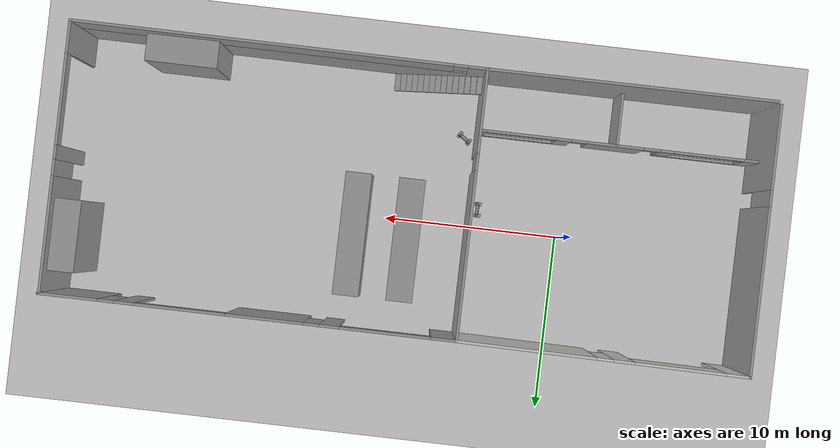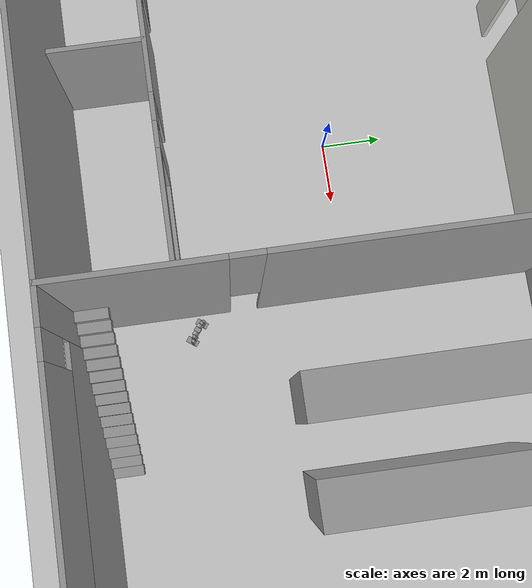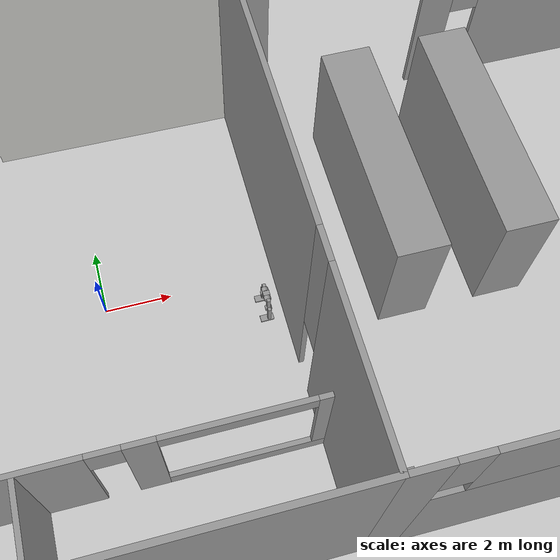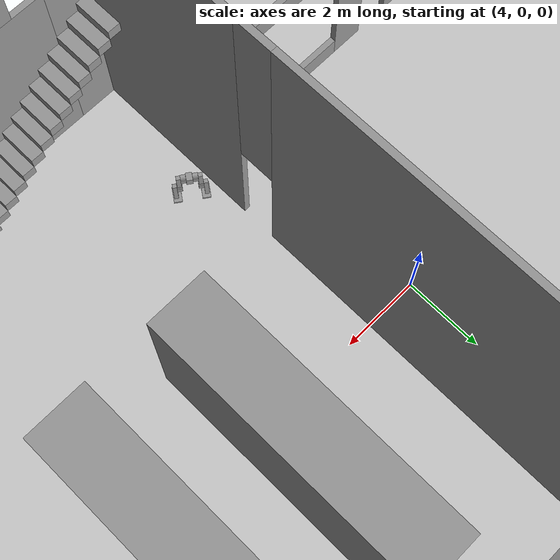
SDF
<sdf version="1.6">
 <world name="default">
  <plugin name="welcome_message" filename="libwelcome_message.so"/>
  <light name="sun" type="directional">
   <pose>0 0 10 0 -0 0</pose>
   <diffuse>0.8 0.8 0.8 1</diffuse>
   <specular>0.2 0.2 0.2 1</specular>
   <attenuation>
    <range>1000</range>
    <constant>0.9</constant>
    <linear>0.01</linear>
    <quadratic>0.001</quadratic>
   </attenuation>
   <direction>-0.5 0.1 -0.9</direction>
  </light>
  <model name="ground_plane">
   <static>1</static>
   <link name="link">
    <collision name="collision">
     <geometry><plane><normal>0 0 1</normal><size>100 100</size></plane></geometry>
     <surface><friction><ode><mu>100</mu><mu2>50</mu2></ode></friction></surface>
    </collision>
    <visual name="visual">
     <cast_shadows>0</cast_shadows>
     <geometry><plane><normal>0 0 1</normal><size>100 100</size></plane></geometry>
     <material>
      <script><uri>file://media/materials/scripts/gazebo.material</uri><name>Gazebo/Grey</name></script>
     </material>
    </visual>
   </link>
  </model>
  <gravity>0 0 -9.8</gravity>
  <magnetic_field>6e-06 2.3e-05 -4.2e-05</magnetic_field>
  <atmosphere type="adiabatic"/>
  <physics name="default_physics" default="0" type="ode">
   <max_step_size>0.001</max_step_size>
   <real_time_factor>1</real_time_factor>
   <real_time_update_rate>1000</real_time_update_rate>
  </physics>
  <scene><ambient>0.4 0.4 0.4 1</ambient><background>0.7 0.7 0.7 1</background><shadows>1</shadows></scene>
  <spherical_coordinates>
   <surface_model>EARTH_WGS84</surface_model>
   <latitude_deg>0</latitude_deg>
   <longitude_deg>0</longitude_deg>
   <elevation>0</elevation>
   <heading_deg>0</heading_deg>
  </spherical_coordinates>
  <model name="TD">
   <pose>8.65214 -1.10284 0 0 -0 0</pose>
   <link name="Stairs_4">
    <visual name="Stairs_4_Visual_0">
     <pose>1.53438 -6.89619 0.133333 0 -0 -1.5708</pose>
     <geometry><box><size>1 0.333333 0.266667</size></box></geometry>
     <material>
      <script><uri>file://media/materials/scripts/gazebo.material</uri><name>Gazebo/Grey</name></script>
      <ambient>1 1 1 1</ambient>
     </material>
     <meta><layer>0</layer></meta>
    </visual>
    <collision name="Stairs_4_Collision_0">
     <geometry><box><size>1 0.333333 0.266667</size></box></geometry>
     <pose>1.53438 -6.89619 0.133333 0 -0 -1.5708</pose>
    </collision>
    <visual name="Stairs_4_Visual_1">
     <pose>1.20105 -6.89619 0.4 0 -0 -1.5708</pose>
     <geometry><box><size>1 0.333333 0.266667</size></box></geometry>
     <material>
      <script><uri>file://media/materials/scripts/gazebo.material</uri><name>Gazebo/Grey</name></script>
      <ambient>1 1 1 1</ambient>
     </material>
     <meta><layer>0</layer></meta>
    </visual>
    <collision name="Stairs_4_Collision_1">
     <geometry><box><size>1 0.333333 0.266667</size></box></geometry>
     <pose>1.20105 -6.89619 0.4 0 -0 -1.5708</pose>
    </collision>
    <visual name="Stairs_4_Visual_2">
     <pose>0.867717 -6.89619 0.666667 0 -0 -1.5708</pose>
     <geometry><box><size>1 0.333333 0.266667</size></box></geometry>
     <material>
      <script><uri>file://media/materials/scripts/gazebo.material</uri><name>Gazebo/Grey</name></script>
      <ambient>1 1 1 1</ambient>
     </material>
     <meta><layer>0</layer></meta>
    </visual>
    <collision name="Stairs_4_Collision_2">
     <geometry><box><size>1 0.333333 0.266667</size></box></geometry>
     <pose>0.867717 -6.89619 0.666667 0 -0 -1.5708</pose>
    </collision>
    <visual name="Stairs_4_Visual_3">
     <pose>0.534383 -6.89619 0.933333 0 -0 -1.5708</pose>
     <geometry><box><size>1 0.333333 0.266667</size></box></geometry>
     <material>
      <script><uri>file://media/materials/scripts/gazebo.material</uri><name>Gazebo/Grey</name></script>
      <ambient>1 1 1 1</ambient>
     </material>
     <meta><layer>0</layer></meta>
    </visual>
    <collision name="Stairs_4_Collision_3">
     <geometry><box><size>1 0.333333 0.266667</size></box></geometry>
     <pose>0.534383 -6.89619 0.933333 0 -0 -1.5708</pose>
    </collision>
    <visual name="Stairs_4_Visual_4">
     <pose>0.201051 -6.89619 1.2 0 -0 -1.5708</pose>
     <geometry><box><size>1 0.333333 0.266667</size></box></geometry>
     <material>
      <script><uri>file://media/materials/scripts/gazebo.material</uri><name>Gazebo/Grey</name></script>
      <ambient>1 1 1 1</ambient>
     </material>
     <meta><layer>0</layer></meta>
    </visual>
    <collision name="Stairs_4_Collision_4">
     <geometry><box><size>1 0.333333 0.266667</size></box></geometry>
     <pose>0.201051 -6.89619 1.2 0 -0 -1.5708</pose>
    </collision>
    <visual name="Stairs_4_Visual_5">
     <pose>-0.132283 -6.89619 1.46667 0 -0 -1.5708</pose>
     <geometry><box><size>1 0.333333 0.266667</size></box></geometry>
     <material>
      <script><uri>file://media/materials/scripts/gazebo.material</uri><name>Gazebo/Grey</name></script>
      <ambient>1 1 1 1</ambient>
     </material>
     <meta><layer>0</layer></meta>
    </visual>
    <collision name="Stairs_4_Collision_5">
     <geometry><box><size>1 0.333333 0.266667</size></box></geometry>
     <pose>-0.132283 -6.89619 1.46667 0 -0 -1.5708</pose>
    </collision>
    <visual name="Stairs_4_Visual_6">
     <pose>-0.465617 -6.89619 1.73333 0 -0 -1.5708</pose>
     <geometry><box><size>1 0.333333 0.266667</size></box></geometry>
     <material>
      <script><uri>file://media/materials/scripts/gazebo.material</uri><name>Gazebo/Grey</name></script>
      <ambient>1 1 1 1</ambient>
     </material>
     <meta><layer>0</layer></meta>
    </visual>
    <collision name="Stairs_4_Collision_6">
     <geometry><box><size>1 0.333333 0.266667</size></box></geometry>
     <pose>-0.465617 -6.89619 1.73333 0 -0 -1.5708</pose>
    </collision>
    <visual name="Stairs_4_Visual_7">
     <pose>-0.79895 -6.89619 2 0 -0 -1.5708</pose>
     <geometry><box><size>1 0.333333 0.266667</size></box></geometry>
     <material>
      <script><uri>file://media/materials/scripts/gazebo.material</uri><name>Gazebo/Grey</name></script>
      <ambient>1 1 1 1</ambient>
     </material>
     <meta><layer>0</layer></meta>
    </visual>
    <collision name="Stairs_4_Collision_7">
     <geometry><box><size>1 0.333333 0.266667</size></box></geometry>
     <pose>-0.79895 -6.89619 2 0 -0 -1.5708</pose>
    </collision>
    <visual name="Stairs_4_Visual_8">
     <pose>-1.13228 -6.89619 2.26667 0 -0 -1.5708</pose>
     <geometry><box><size>1 0.333333 0.266667</size></box></geometry>
     <material>
      <script><uri>file://media/materials/scripts/gazebo.material</uri><name>Gazebo/Grey</name></script>
      <ambient>1 1 1 1</ambient>
     </material>
     <meta><layer>0</layer></meta>
    </visual>
    <collision name="Stairs_4_Collision_8">
     <geometry><box><size>1 0.333333 0.266667</size></box></geometry>
     <pose>-1.13228 -6.89619 2.26667 0 -0 -1.5708</pose>
    </collision>
    <visual name="Stairs_4_Visual_9">
     <pose>-1.46562 -6.89619 2.53333 0 -0 -1.5708</pose>
     <geometry><box><size>1 0.333333 0.266667</size></box></geometry>
     <material>
      <script><uri>file://media/materials/scripts/gazebo.material</uri><name>Gazebo/Grey</name></script>
      <ambient>1 1 1 1</ambient>
     </material>
     <meta><layer>0</layer></meta>
    </visual>
    <collision name="Stairs_4_Collision_9">
     <geometry><box><size>1 0.333333 0.266667</size></box></geometry>
     <pose>-1.46562 -6.89619 2.53333 0 -0 -1.5708</pose>
    </collision>
    <visual name="Stairs_4_Visual_10">
     <pose>-1.79895 -6.89619 2.8 0 -0 -1.5708</pose>
     <geometry><box><size>1 0.333333 0.266667</size></box></geometry>
     <material>
      <script><uri>file://media/materials/scripts/gazebo.material</uri><name>Gazebo/Grey</name></script>
      <ambient>1 1 1 1</ambient>
     </material>
     <meta><layer>0</layer></meta>
    </visual>
    <collision name="Stairs_4_Collision_10">
     <geometry><box><size>1 0.333333 0.266667</size></box></geometry>
     <pose>-1.79895 -6.89619 2.8 0 -0 -1.5708</pose>
    </collision>
    <visual name="Stairs_4_Visual_11">
     <pose>-2.13228 -6.89619 3.06667 0 -0 -1.5708</pose>
     <geometry><box><size>1 0.333333 0.266667</size></box></geometry>
     <material>
      <script><uri>file://media/materials/scripts/gazebo.material</uri><name>Gazebo/Grey</name></script>
      <ambient>1 1 1 1</ambient>
     </material>
     <meta><layer>0</layer></meta>
    </visual>
    <collision name="Stairs_4_Collision_11">
     <geometry><box><size>1 0.333333 0.266667</size></box></geometry>
     <pose>-2.13228 -6.89619 3.06667 0 -0 -1.5708</pose>
    </collision>
    <visual name="Stairs_4_Visual_12">
     <pose>-2.46562 -6.89619 3.33333 0 -0 -1.5708</pose>
     <geometry><box><size>1 0.333333 0.266667</size></box></geometry>
     <material>
      <script><uri>file://media/materials/scripts/gazebo.material</uri><name>Gazebo/Grey</name></script>
      <ambient>1 1 1 1</ambient>
     </material>
     <meta><layer>0</layer></meta>
    </visual>
    <collision name="Stairs_4_Collision_12">
     <geometry><box><size>1 0.333333 0.266667</size></box></geometry>
     <pose>-2.46562 -6.89619 3.33333 0 -0 -1.5708</pose>
    </collision>
    <visual name="Stairs_4_Visual_13">
     <pose>-2.79895 -6.89619 3.6 0 -0 -1.5708</pose>
     <geometry><box><size>1 0.333333 0.266667</size></box></geometry>
     <material>
      <script><uri>file://media/materials/scripts/gazebo.material</uri><name>Gazebo/Grey</name></script>
      <ambient>1 1 1 1</ambient>
     </material>
     <meta><layer>0</layer></meta>
    </visual>
    <collision name="Stairs_4_Collision_13">
     <geometry><box><size>1 0.333333 0.266667</size></box></geometry>
     <pose>-2.79895 -6.89619 3.6 0 -0 -1.5708</pose>
    </collision>
    <visual name="Stairs_4_Visual_14">
     <pose>-3.13228 -6.89619 3.86667 0 -0 -1.5708</pose>
     <geometry><box><size>1 0.333333 0.266667</size></box></geometry>
     <material>
      <script><uri>file://media/materials/scripts/gazebo.material</uri><name>Gazebo/Grey</name></script>
      <ambient>1 1 1 1</ambient>
     </material>
     <meta><layer>0</layer></meta>
    </visual>
    <collision name="Stairs_4_Collision_14">
     <geometry><box><size>1 0.333333 0.266667</size></box></geometry>
     <pose>-3.13228 -6.89619 3.86667 0 -0 -1.5708</pose>
    </collision>
   </link>
   <link name="Wall_0">
    <pose>-11.382 7.45126 0 0 0 -0.008729</pose>
    <visual name="Wall_0_Visual_0">
     <pose>-7.40723 0 4 0 -0 0</pose>
     <geometry><box><size>1.37391 0.15 8</size></box></geometry>
     <material>
      <script><uri>file://media/materials/scripts/gazebo.material</uri><name>Gazebo/CeilingTiled</name></script>
      <ambient>1 1 1 1</ambient>
     </material>
     <meta><layer>0</layer></meta>
    </visual>
    <collision name="Wall_0_Collision_0">
     <geometry><box><size>1.37391 0.15 8</size></box></geometry>
     <pose>-7.40723 0 4 0 -0 0</pose>
    </collision>
    <visual name="Wall_0_Visual_1">
     <pose>-1.13343 0 4 0 -0 0</pose>
     <geometry><box><size>1.17368 0.15 8</size></box></geometry>
     <material>
      <script><uri>file://media/materials/scripts/gazebo.material</uri><name>Gazebo/CeilingTiled</name></script>
      <ambient>1 1 1 1</ambient>
     </material>
     <meta><layer>0</layer></meta>
    </visual>
    <collision name="Wall_0_Collision_1">
     <geometry><box><size>1.17368 0.15 8</size></box></geometry>
     <pose>-1.13343 0 4 0 -0 0</pose>
    </collision>
    <visual name="Wall_0_Visual_2">
     <pose>4.22379 0 4 0 -0 0</pose>
     <geometry><box><size>7.74078 0.15 8</size></box></geometry>
     <material>
      <script><uri>file://media/materials/scripts/gazebo.material</uri><name>Gazebo/CeilingTiled</name></script>
      <ambient>1 1 1 1</ambient>
     </material>
     <meta><layer>0</layer></meta>
    </visual>
    <collision name="Wall_0_Collision_2">
     <geometry><box><size>7.74078 0.15 8</size></box></geometry>
     <pose>4.22379 0 4 0 -0 0</pose>
    </collision>
    <visual name="Wall_0_Visual_3">
     <pose>-0.096596 0 5.5 0 -0 0</pose>
     <geometry><box><size>0.9 0.15 5</size></box></geometry>
     <material>
      <script><uri>file://media/materials/scripts/gazebo.material</uri><name>Gazebo/CeilingTiled</name></script>
      <ambient>1 1 1 1</ambient>
     </material>
     <meta><layer>0</layer></meta>
    </visual>
    <collision name="Wall_0_Collision_3">
     <geometry><box><size>0.9 0.15 5</size></box></geometry>
     <pose>-0.096596 0 5.5 0 -0 0</pose>
    </collision>
    <visual name="Wall_0_Visual_4">
     <pose>-4.22027 0 6.5 0 -0 0</pose>
     <geometry><box><size>5 0.15 3</size></box></geometry>
     <material>
      <script><uri>file://media/materials/scripts/gazebo.material</uri><name>Gazebo/CeilingTiled</name></script>
      <ambient>1 1 1 1</ambient>
     </material>
     <meta><layer>0</layer></meta>
    </visual>
    <collision name="Wall_0_Collision_4">
     <geometry><box><size>5 0.15 3</size></box></geometry>
     <pose>-4.22027 0 6.5 0 -0 0</pose>
    </collision>
   </link>
   <link name="Wall_10">
    <pose>-3.363 -0.043236 0 0 0 -1.5708</pose>
    <visual name="Wall_10_Visual_0">
     <pose>-2.78601 0 4 0 -0 0</pose>
     <geometry><box><size>9.42697 0.15 8</size></box></geometry>
     <material>
      <script><uri>file://media/materials/scripts/gazebo.material</uri><name>Gazebo/Grey</name></script>
      <ambient>1 1 1 1</ambient>
     </material>
     <meta><layer>0</layer></meta>
    </visual>
    <collision name="Wall_10_Collision_0">
     <geometry><box><size>9.42697 0.15 8</size></box></geometry>
     <pose>-2.78601 0 4 0 -0 0</pose>
    </collision>
    <visual name="Wall_10_Visual_1">
     <pose>5.16348 0 4 0 -0 0</pose>
     <geometry><box><size>4.67203 0.15 8</size></box></geometry>
     <material>
      <script><uri>file://media/materials/scripts/gazebo.material</uri><name>Gazebo/Grey</name></script>
      <ambient>1 1 1 1</ambient>
     </material>
     <meta><layer>0</layer></meta>
    </visual>
    <collision name="Wall_10_Collision_1">
     <geometry><box><size>4.67203 0.15 8</size></box></geometry>
     <pose>5.16348 0 4 0 -0 0</pose>
    </collision>
    <visual name="Wall_10_Visual_2">
     <pose>2.37747 0 5.5 0 -0 0</pose>
     <geometry><box><size>0.9 0.15 5</size></box></geometry>
     <material>
      <script><uri>file://media/materials/scripts/gazebo.material</uri><name>Gazebo/Grey</name></script>
      <ambient>1 1 1 1</ambient>
     </material>
     <meta><layer>0</layer></meta>
    </visual>
    <collision name="Wall_10_Collision_2">
     <geometry><box><size>0.9 0.15 5</size></box></geometry>
     <pose>2.37747 0 5.5 0 -0 0</pose>
    </collision>
   </link>
   <link name="Wall_13">
    <collision name="Wall_13_Collision">
     <geometry><box><size>16 0.15 8</size></box></geometry>
     <pose>0 0 4 0 -0 0</pose>
    </collision>
    <visual name="Wall_13_Visual">
     <pose>0 0 4 0 -0 0</pose>
     <geometry><box><size>16 0.15 8</size></box></geometry>
     <material>
      <script><uri>file://media/materials/scripts/gazebo.material</uri><name>Gazebo/Grey</name></script>
      <ambient>1 1 1 1</ambient>
     </material>
     <meta><layer>0</layer></meta>
    </visual>
    <pose>-11.288 -7.49124 0 0 0 -3.13863</pose>
   </link>
   <link name="Wall_15">
    <pose>-11.437 -4.40674 0 0 -0 0</pose>
    <visual name="Wall_15_Visual_0">
     <pose>-7.59892 0 2 0 -0 0</pose>
     <geometry><box><size>1.05216 0.15 4</size></box></geometry>
     <material>
      <script><uri>file://media/materials/scripts/gazebo.material</uri><name>Gazebo/Grey</name></script>
      <ambient>1 1 1 1</ambient>
     </material>
     <meta><layer>0</layer></meta>
    </visual>
    <collision name="Wall_15_Collision_0">
     <geometry><box><size>1.05216 0.15 4</size></box></geometry>
     <pose>-7.59892 0 2 0 -0 0</pose>
    </collision>
    <visual name="Wall_15_Visual_1">
     <pose>0.254519 0 2 0 -0 0</pose>
     <geometry><box><size>3.24063 0.15 4</size></box></geometry>
     <material>
      <script><uri>file://media/materials/scripts/gazebo.material</uri><name>Gazebo/Grey</name></script>
      <ambient>1 1 1 1</ambient>
     </material>
     <meta><layer>0</layer></meta>
    </visual>
    <collision name="Wall_15_Collision_1">
     <geometry><box><size>3.24063 0.15 4</size></box></geometry>
     <pose>0.254519 0 2 0 -0 0</pose>
    </collision>
    <visual name="Wall_15_Visual_2">
     <pose>3.20125 0 2 0 -0 0</pose>
     <geometry><box><size>0.852824 0.15 4</size></box></geometry>
     <material>
      <script><uri>file://media/materials/scripts/gazebo.material</uri><name>Gazebo/Grey</name></script>
      <ambient>1 1 1 1</ambient>
     </material>
     <meta><layer>0</layer></meta>
    </visual>
    <collision name="Wall_15_Collision_2">
     <geometry><box><size>0.852824 0.15 4</size></box></geometry>
     <pose>3.20125 0 2 0 -0 0</pose>
    </collision>
    <visual name="Wall_15_Visual_3">
     <pose>-4.66932 0 0.25 0 -0 0</pose>
     <geometry><box><size>4.80705 0.15 0.5</size></box></geometry>
     <material>
      <script><uri>file://media/materials/scripts/gazebo.material</uri><name>Gazebo/Grey</name></script>
      <ambient>1 1 1 1</ambient>
     </material>
     <meta><layer>0</layer></meta>
    </visual>
    <collision name="Wall_15_Collision_3">
     <geometry><box><size>4.80705 0.15 0.5</size></box></geometry>
     <pose>-4.66932 0 0.25 0 -0 0</pose>
    </collision>
    <visual name="Wall_15_Visual_4">
     <pose>5.87633 0 0.25 0 -0 0</pose>
     <geometry><box><size>4.49734 0.15 0.5</size></box></geometry>
     <material>
      <script><uri>file://media/materials/scripts/gazebo.material</uri><name>Gazebo/Grey</name></script>
      <ambient>1 1 1 1</ambient>
     </material>
     <meta><layer>0</layer></meta>
    </visual>
    <collision name="Wall_15_Collision_4">
     <geometry><box><size>4.49734 0.15 0.5</size></box></geometry>
     <pose>5.87633 0 0.25 0 -0 0</pose>
    </collision>
    <visual name="Wall_15_Visual_5">
     <pose>-2.66932 0 2.25 0 -0 0</pose>
     <geometry><box><size>0.807047 0.15 3.5</size></box></geometry>
     <material>
      <script><uri>file://media/materials/scripts/gazebo.material</uri><name>Gazebo/Grey</name></script>
      <ambient>1 1 1 1</ambient>
     </material>
     <meta><layer>0</layer></meta>
    </visual>
    <collision name="Wall_15_Collision_5">
     <geometry><box><size>0.807047 0.15 3.5</size></box></geometry>
     <pose>-2.66932 0 2.25 0 -0 0</pose>
    </collision>
    <visual name="Wall_15_Visual_6">
     <pose>-2.66932 0 2.25 0 -0 0</pose>
     <geometry><box><size>0.807047 0.15 3.5</size></box></geometry>
     <material>
      <script><uri>file://media/materials/scripts/gazebo.material</uri><name>Gazebo/Grey</name></script>
      <ambient>1 1 1 1</ambient>
     </material>
     <meta><layer>0</layer></meta>
    </visual>
    <collision name="Wall_15_Collision_6">
     <geometry><box><size>0.807047 0.15 3.5</size></box></geometry>
     <pose>-2.66932 0 2.25 0 -0 0</pose>
    </collision>
    <visual name="Wall_15_Visual_7">
     <pose>7.87633 0 2.25 0 -0 0</pose>
     <geometry><box><size>0.497343 0.15 3.5</size></box></geometry>
     <material>
      <script><uri>file://media/materials/scripts/gazebo.material</uri><name>Gazebo/Grey</name></script>
      <ambient>1 1 1 1</ambient>
     </material>
     <meta><layer>0</layer></meta>
    </visual>
    <collision name="Wall_15_Collision_7">
     <geometry><box><size>0.497343 0.15 3.5</size></box></geometry>
     <pose>7.87633 0 2.25 0 -0 0</pose>
    </collision>
    <visual name="Wall_15_Visual_8">
     <pose>2.32483 0 3.5 0 -0 0</pose>
     <geometry><box><size>0.9 0.15 1</size></box></geometry>
     <material>
      <script><uri>file://media/materials/scripts/gazebo.material</uri><name>Gazebo/Grey</name></script>
      <ambient>1 1 1 1</ambient>
     </material>
     <meta><layer>0</layer></meta>
    </visual>
    <collision name="Wall_15_Collision_8">
     <geometry><box><size>0.9 0.15 1</size></box></geometry>
     <pose>2.32483 0 3.5 0 -0 0</pose>
    </collision>
    <visual name="Wall_15_Visual_9">
     <pose>-1.8158 0 3.5 0 -0 0</pose>
     <geometry><box><size>0.9 0.15 1</size></box></geometry>
     <material>
      <script><uri>file://media/materials/scripts/gazebo.material</uri><name>Gazebo/Grey</name></script>
      <ambient>1 1 1 1</ambient>
     </material>
     <meta><layer>0</layer></meta>
    </visual>
    <collision name="Wall_15_Collision_9">
     <geometry><box><size>0.9 0.15 1</size></box></geometry>
     <pose>-1.8158 0 3.5 0 -0 0</pose>
    </collision>
    <visual name="Wall_15_Visual_10">
     <pose>-1.8158 0 3.5 0 -0 0</pose>
     <geometry><box><size>0.9 0.15 1</size></box></geometry>
     <material>
      <script><uri>file://media/materials/scripts/gazebo.material</uri><name>Gazebo/Grey</name></script>
      <ambient>1 1 1 1</ambient>
     </material>
     <meta><layer>0</layer></meta>
    </visual>
    <collision name="Wall_15_Collision_10">
     <geometry><box><size>0.9 0.15 1</size></box></geometry>
     <pose>-1.8158 0 3.5 0 -0 0</pose>
    </collision>
    <visual name="Wall_15_Visual_11">
     <pose>-5.07284 0 3.75 0 -0 0</pose>
     <geometry><box><size>4 0.15 0.5</size></box></geometry>
     <material>
      <script><uri>file://media/materials/scripts/gazebo.material</uri><name>Gazebo/Grey</name></script>
      <ambient>1 1 1 1</ambient>
     </material>
     <meta><layer>0</layer></meta>
    </visual>
    <collision name="Wall_15_Collision_11">
     <geometry><box><size>4 0.15 0.5</size></box></geometry>
     <pose>-5.07284 0 3.75 0 -0 0</pose>
    </collision>
    <visual name="Wall_15_Visual_12">
     <pose>5.62766 0 3.75 0 -0 0</pose>
     <geometry><box><size>4 0.15 0.5</size></box></geometry>
     <material>
      <script><uri>file://media/materials/scripts/gazebo.material</uri><name>Gazebo/Grey</name></script>
      <ambient>1 1 1 1</ambient>
     </material>
     <meta><layer>0</layer></meta>
    </visual>
    <collision name="Wall_15_Collision_12">
     <geometry><box><size>4 0.15 0.5</size></box></geometry>
     <pose>5.62766 0 3.75 0 -0 0</pose>
    </collision>
   </link>
   <link name="Wall_17">
    <collision name="Wall_17_Collision">
     <geometry><box><size>3 0.15 4</size></box></geometry>
     <pose>0 0 2 0 -0 0</pose>
    </collision>
    <visual name="Wall_17_Visual">
     <pose>0 0 2 0 -0 0</pose>
     <geometry><box><size>3 0.15 4</size></box></geometry>
     <material>
      <script><uri>file://media/materials/scripts/gazebo.material</uri><name>Gazebo/Grey</name></script>
      <ambient>1 1 1 1</ambient>
     </material>
     <meta><layer>0</layer></meta>
    </visual>
    <pose>-11.253 -5.87874 0 0 0 -1.5708</pose>
   </link>
   <link name="Wall_19">
    <pose>8.062 7.38126 0 0 -0 0</pose>
    <visual name="Wall_19_Visual_0">
     <pose>-10.7556 0 4 0 -0 0</pose>
     <geometry><box><size>1.48881 0.15 8</size></box></geometry>
     <material>
      <script><uri>file://media/materials/scripts/gazebo.material</uri><name>Gazebo/Grey</name></script>
      <ambient>1 1 1 1</ambient>
     </material>
     <meta><layer>0</layer></meta>
    </visual>
    <collision name="Wall_19_Collision_0">
     <geometry><box><size>1.48881 0.15 8</size></box></geometry>
     <pose>-10.7556 0 4 0 -0 0</pose>
    </collision>
    <visual name="Wall_19_Visual_1">
     <pose>-4.47985 0 4 0 -0 0</pose>
     <geometry><box><size>1.06269 0.15 8</size></box></geometry>
     <material>
      <script><uri>file://media/materials/scripts/gazebo.material</uri><name>Gazebo/Grey</name></script>
      <ambient>1 1 1 1</ambient>
     </material>
     <meta><layer>0</layer></meta>
    </visual>
    <collision name="Wall_19_Collision_1">
     <geometry><box><size>1.06269 0.15 8</size></box></geometry>
     <pose>-4.47985 0 4 0 -0 0</pose>
    </collision>
    <visual name="Wall_19_Visual_2">
     <pose>-0.912084 0 4 0 -0 0</pose>
     <geometry><box><size>4.27284 0.15 8</size></box></geometry>
     <material>
      <script><uri>file://media/materials/scripts/gazebo.material</uri><name>Gazebo/Grey</name></script>
      <ambient>1 1 1 1</ambient>
     </material>
     <meta><layer>0</layer></meta>
    </visual>
    <collision name="Wall_19_Collision_2">
     <geometry><box><size>4.27284 0.15 8</size></box></geometry>
     <pose>-0.912084 0 4 0 -0 0</pose>
    </collision>
    <visual name="Wall_19_Visual_3">
     <pose>6.75568 0 4 0 -0 0</pose>
     <geometry><box><size>1.06269 0.15 8</size></box></geometry>
     <material>
      <script><uri>file://media/materials/scripts/gazebo.material</uri><name>Gazebo/Grey</name></script>
      <ambient>1 1 1 1</ambient>
     </material>
     <meta><layer>0</layer></meta>
    </visual>
    <collision name="Wall_19_Collision_3">
     <geometry><box><size>1.06269 0.15 8</size></box></geometry>
     <pose>6.75568 0 4 0 -0 0</pose>
    </collision>
    <visual name="Wall_19_Visual_4">
     <pose>9.84351 0 4 0 -0 0</pose>
     <geometry><box><size>3.31298 0.15 8</size></box></geometry>
     <material>
      <script><uri>file://media/materials/scripts/gazebo.material</uri><name>Gazebo/Grey</name></script>
      <ambient>1 1 1 1</ambient>
     </material>
     <meta><layer>0</layer></meta>
    </visual>
    <collision name="Wall_19_Collision_4">
     <geometry><box><size>3.31298 0.15 8</size></box></geometry>
     <pose>9.84351 0 4 0 -0 0</pose>
    </collision>
    <visual name="Wall_19_Visual_5">
     <pose>-3.4985 0 5.5 0 -0 0</pose>
     <geometry><box><size>0.9 0.15 5</size></box></geometry>
     <material>
      <script><uri>file://media/materials/scripts/gazebo.material</uri><name>Gazebo/Grey</name></script>
      <ambient>1 1 1 1</ambient>
     </material>
     <meta><layer>0</layer></meta>
    </visual>
    <collision name="Wall_19_Collision_5">
     <geometry><box><size>0.9 0.15 5</size></box></geometry>
     <pose>-3.4985 0 5.5 0 -0 0</pose>
    </collision>
    <visual name="Wall_19_Visual_6">
     <pose>7.73702 0 5.5 0 -0 0</pose>
     <geometry><box><size>0.9 0.15 5</size></box></geometry>
     <material>
      <script><uri>file://media/materials/scripts/gazebo.material</uri><name>Gazebo/Grey</name></script>
      <ambient>1 1 1 1</ambient>
     </material>
     <meta><layer>0</layer></meta>
    </visual>
    <collision name="Wall_19_Collision_6">
     <geometry><box><size>0.9 0.15 5</size></box></geometry>
     <pose>7.73702 0 5.5 0 -0 0</pose>
    </collision>
    <visual name="Wall_19_Visual_7">
     <pose>-7.51119 0 7.5 0 -0 0</pose>
     <geometry><box><size>5 0.15 1</size></box></geometry>
     <material>
      <script><uri>file://media/materials/scripts/gazebo.material</uri><name>Gazebo/Grey</name></script>
      <ambient>1 1 1 1</ambient>
     </material>
     <meta><layer>0</layer></meta>
    </visual>
    <collision name="Wall_19_Collision_7">
     <geometry><box><size>5 0.15 1</size></box></geometry>
     <pose>-7.51119 0 7.5 0 -0 0</pose>
    </collision>
    <visual name="Wall_19_Visual_8">
     <pose>3.72433 0 7.5 0 -0 0</pose>
     <geometry><box><size>5 0.15 1</size></box></geometry>
     <material>
      <script><uri>file://media/materials/scripts/gazebo.material</uri><name>Gazebo/Grey</name></script>
      <ambient>1 1 1 1</ambient>
     </material>
     <meta><layer>0</layer></meta>
    </visual>
    <collision name="Wall_19_Collision_8">
     <geometry><box><size>5 0.15 1</size></box></geometry>
     <pose>3.72433 0 7.5 0 -0 0</pose>
    </collision>
   </link>
   <link name="Wall_21">
    <pose>8.035 -7.49474 0 0 0 -0.002369</pose>
    <visual name="Wall_21_Visual_0">
     <pose>-10.9086 0 4 0 -0 0</pose>
     <geometry><box><size>1.12989 0.15 8</size></box></geometry>
     <material>
      <script><uri>file://media/materials/scripts/gazebo.material</uri><name>Gazebo/Grey</name></script>
      <ambient>1 1 1 1</ambient>
     </material>
     <meta><layer>0</layer></meta>
    </visual>
    <collision name="Wall_21_Collision_0">
     <geometry><box><size>1.12989 0.15 8</size></box></geometry>
     <pose>-10.9086 0 4 0 -0 0</pose>
    </collision>
    <visual name="Wall_21_Visual_1">
     <pose>0.564943 0 2.5 0 -0 0</pose>
     <geometry><box><size>21.8172 0.15 5</size></box></geometry>
     <material>
      <script><uri>file://media/materials/scripts/gazebo.material</uri><name>Gazebo/Grey</name></script>
      <ambient>1 1 1 1</ambient>
     </material>
     <meta><layer>0</layer></meta>
    </visual>
    <collision name="Wall_21_Collision_1">
     <geometry><box><size>21.8172 0.15 5</size></box></geometry>
     <pose>0.564943 0 2.5 0 -0 0</pose>
    </collision>
    <visual name="Wall_21_Visual_2">
     <pose>0.964943 0 6.5 0 -0 0</pose>
     <geometry><box><size>21.0172 0.15 3</size></box></geometry>
     <material>
      <script><uri>file://media/materials/scripts/gazebo.material</uri><name>Gazebo/Grey</name></script>
      <ambient>1 1 1 1</ambient>
     </material>
     <meta><layer>0</layer></meta>
    </visual>
    <collision name="Wall_21_Collision_2">
     <geometry><box><size>21.0172 0.15 3</size></box></geometry>
     <pose>0.964943 0 6.5 0 -0 0</pose>
    </collision>
    <visual name="Wall_21_Visual_3">
     <pose>-9.94365 0 6.9 0 -0 0</pose>
     <geometry><box><size>0.8 0.15 2.2</size></box></geometry>
     <material>
      <script><uri>file://media/materials/scripts/gazebo.material</uri><name>Gazebo/Grey</name></script>
      <ambient>1 1 1 1</ambient>
     </material>
     <meta><layer>0</layer></meta>
    </visual>
    <collision name="Wall_21_Collision_3">
     <geometry><box><size>0.8 0.15 2.2</size></box></geometry>
     <pose>-9.94365 0 6.9 0 -0 0</pose>
    </collision>
   </link>
   <link name="Wall_55">
    <pose>19.433 -0.096736 0 0 -0 1.5708</pose>
    <visual name="Wall_55_Visual_0">
     <pose>-6.56325 0 4 0 -0 0</pose>
     <geometry><box><size>1.87349 0.15 8</size></box></geometry>
     <material>
      <script><uri>file://media/materials/scripts/gazebo.material</uri><name>Gazebo/Grey</name></script>
      <ambient>1 1 1 1</ambient>
     </material>
     <meta><layer>0</layer></meta>
    </visual>
    <collision name="Wall_55_Collision_0">
     <geometry><box><size>1.87349 0.15 8</size></box></geometry>
     <pose>-6.56325 0 4 0 -0 0</pose>
    </collision>
    <visual name="Wall_55_Visual_1">
     <pose>-0.22892 0 4 0 -0 0</pose>
     <geometry><box><size>0.795175 0.15 8</size></box></geometry>
     <material>
      <script><uri>file://media/materials/scripts/gazebo.material</uri><name>Gazebo/Grey</name></script>
      <ambient>1 1 1 1</ambient>
     </material>
     <meta><layer>0</layer></meta>
    </visual>
    <collision name="Wall_55_Collision_1">
     <geometry><box><size>0.795175 0.15 8</size></box></geometry>
     <pose>-0.22892 0 4 0 -0 0</pose>
    </collision>
    <visual name="Wall_55_Visual_2">
     <pose>4.28433 0 4 0 -0 0</pose>
     <geometry><box><size>6.43133 0.15 8</size></box></geometry>
     <material>
      <script><uri>file://media/materials/scripts/gazebo.material</uri><name>Gazebo/Grey</name></script>
      <ambient>1 1 1 1</ambient>
     </material>
     <meta><layer>0</layer></meta>
    </visual>
    <collision name="Wall_55_Collision_2">
     <geometry><box><size>6.43133 0.15 8</size></box></geometry>
     <pose>4.28433 0 4 0 -0 0</pose>
    </collision>
    <visual name="Wall_55_Visual_3">
     <pose>0.618668 0 5.5 0 -0 0</pose>
     <geometry><box><size>0.9 0.15 5</size></box></geometry>
     <material>
      <script><uri>file://media/materials/scripts/gazebo.material</uri><name>Gazebo/Grey</name></script>
      <ambient>1 1 1 1</ambient>
     </material>
     <meta><layer>0</layer></meta>
    </visual>
    <collision name="Wall_55_Collision_3">
     <geometry><box><size>0.9 0.15 5</size></box></geometry>
     <pose>0.618668 0 5.5 0 -0 0</pose>
    </collision>
    <visual name="Wall_55_Visual_4">
     <pose>-3.12651 0 7.5 0 -0 0</pose>
     <geometry><box><size>5 0.15 1</size></box></geometry>
     <material>
      <script><uri>file://media/materials/scripts/gazebo.material</uri><name>Gazebo/Grey</name></script>
      <ambient>1 1 1 1</ambient>
     </material>
     <meta><layer>0</layer></meta>
    </visual>
    <collision name="Wall_55_Collision_4">
     <geometry><box><size>5 0.15 1</size></box></geometry>
     <pose>-3.12651 0 7.5 0 -0 0</pose>
    </collision>
   </link>
   <link name="Wall_57">
    <collision name="Wall_57_Collision">
     <geometry><box><size>7 1.5 4</size></box></geometry>
     <pose>0 0 2 0 -0 0</pose>
    </collision>
    <visual name="Wall_57_Visual">
     <pose>0 0 2 0 -0 0</pose>
     <geometry><box><size>7 1.5 4</size></box></geometry>
     <material>
      <script><uri>file://media/materials/scripts/gazebo.material</uri><name>Gazebo/Grey</name></script>
      <ambient>1 1 1 1</ambient>
     </material>
     <meta><layer>0</layer></meta>
    </visual>
    <pose>0.015483 2.25582 0 0 -0 1.5708</pose>
   </link>
   <link name="Wall_60">
    <collision name="Wall_60_Collision">
     <geometry><box><size>7 1.5 4</size></box></geometry>
     <pose>0 0 2 0 -0 0</pose>
    </collision>
    <visual name="Wall_60_Visual">
     <pose>0 0 2 0 -0 0</pose>
     <geometry><box><size>7 1.5 4</size></box></geometry>
     <material>
      <script><uri>file://media/materials/scripts/gazebo.material</uri><name>Gazebo/Grey</name></script>
      <ambient>1 1 1 1</ambient>
     </material>
     <meta><layer>0</layer></meta>
    </visual>
    <pose>3.06551 2.2558 0 0 -0 1.5708</pose>
   </link>
   <link name="Wall_62">
    <collision name="Wall_62_Collision">
     <geometry><box><size>4 1.5 7</size></box></geometry>
     <pose>0 0 3.5 0 -0 0</pose>
    </collision>
    <visual name="Wall_62_Visual">
     <pose>0 0 3.5 0 -0 0</pose>
     <geometry><box><size>4 1.5 7</size></box></geometry>
     <material>
      <script><uri>file://media/materials/scripts/gazebo.material</uri><name>Gazebo/Grey</name></script>
      <ambient>1 1 1 1</ambient>
     </material>
     <meta><layer>0</layer></meta>
    </visual>
    <pose>18.635 4.12585 0 0 -0 1.5708</pose>
   </link>
   <link name="Wall_64">
    <collision name="Wall_64_Collision">
     <geometry><box><size>4 1.5 7</size></box></geometry>
     <pose>0 0 3.5 0 -0 0</pose>
    </collision>
    <visual name="Wall_64_Visual">
     <pose>0 0 3.5 0 -0 0</pose>
     <geometry><box><size>4 1.5 7</size></box></geometry>
     <material>
      <script><uri>file://media/materials/scripts/gazebo.material</uri><name>Gazebo/Grey</name></script>
      <ambient>1 1 1 1</ambient>
     </material>
     <meta><layer>0</layer></meta>
    </visual>
    <pose>13.3573 -6.6474 0 0 -0 0</pose>
   </link>
   <link name="Wall_8">
    <pose>-19.401 0.096264 0 0 0 -1.5708</pose>
    <visual name="Wall_8_Visual_0">
     <pose>-2.79355 0 4 0 -0 0</pose>
     <geometry><box><size>9.4129 0.15 8</size></box></geometry>
     <material>
      <script><uri>file://media/materials/scripts/gazebo.material</uri><name>Gazebo/Grey</name></script>
      <ambient>1 1 1 1</ambient>
     </material>
     <meta><layer>0</layer></meta>
    </visual>
    <collision name="Wall_8_Collision_0">
     <geometry><box><size>9.4129 0.15 8</size></box></geometry>
     <pose>-2.79355 0 4 0 -0 0</pose>
    </collision>
    <visual name="Wall_8_Visual_1">
     <pose>5.15645 0 4 0 -0 0</pose>
     <geometry><box><size>4.6871 0.15 8</size></box></geometry>
     <material>
      <script><uri>file://media/materials/scripts/gazebo.material</uri><name>Gazebo/Grey</name></script>
      <ambient>1 1 1 1</ambient>
     </material>
     <meta><layer>0</layer></meta>
    </visual>
    <collision name="Wall_8_Collision_1">
     <geometry><box><size>4.6871 0.15 8</size></box></geometry>
     <pose>5.15645 0 4 0 -0 0</pose>
    </collision>
    <visual name="Wall_8_Visual_2">
     <pose>2.36289 0 5.5 0 -0 0</pose>
     <geometry><box><size>0.9 0.15 5</size></box></geometry>
     <material>
      <script><uri>file://media/materials/scripts/gazebo.material</uri><name>Gazebo/Grey</name></script>
      <ambient>1 1 1 1</ambient>
     </material>
     <meta><layer>0</layer></meta>
    </visual>
    <collision name="Wall_8_Collision_2">
     <geometry><box><size>0.9 0.15 5</size></box></geometry>
     <pose>2.36289 0 5.5 0 -0 0</pose>
    </collision>
   </link>
   <static>1</static>
  </model>
  <model name="humanoid3">
   <link name="link_0_clone">
    <pose>-0.327462 1.23378 -0.128216 0 -0 0</pose>
    <inertial>
     <mass>1</mass>
     <inertia>
      <ixx>0.166667</ixx>
      <ixy>0</ixy>
      <ixz>0</ixz>
      <iyy>0.166667</iyy>
      <iyz>0</iyz>
      <izz>0.166667</izz>
     </inertia>
    </inertial>
    <visual name="visual">
     <geometry><box><size>0.4 0.2 0.05</size></box></geometry>
     <material>
      <lighting>1</lighting>
      <script><uri>file://media/materials/scripts/gazebo.material</uri><name>Gazebo/Grey</name></script>
      <ambient>0.3 0.3 0.3 1</ambient>
      <diffuse>0.7 0.7 0.7 1</diffuse>
      <specular>0.01 0.01 0.01 1</specular>
      <emissive>0 0 0 1</emissive>
      <shader type="vertex"><normal_map>__default__</normal_map></shader>
     </material>
    </visual>
    <collision name="collision">
     <geometry><box><size>0.4 0.2 0.05</size></box></geometry>
     <surface>
      <friction>
       <ode><mu>1</mu><mu2>1</mu2><fdir1>0 0 0</fdir1><slip1>0</slip1><slip2>0</slip2></ode>
       <torsional>
        <coefficient>1</coefficient>
        <patch_radius>0</patch_radius>
        <surface_radius>0</surface_radius>
        <use_patch_radius>1</use_patch_radius>
        <ode><slip>0</slip></ode>
       </torsional>
      </friction>
      <bounce><restitution_coefficient>0</restitution_coefficient><threshold>1e+06</threshold></bounce>
      <contact>
       <collide_without_contact>0</collide_without_contact>
       <collide_without_contact_bitmask>1</collide_without_contact_bitmask>
       <collide_bitmask>1</collide_bitmask>
       <ode>
        <soft_cfm>0</soft_cfm>
        <soft_erp>0.2</soft_erp>
        <kp>1e+13</kp>
        <kd>1</kd>
        <max_vel>0.01</max_vel>
        <min_depth>0</min_depth>
       </ode>
       <bullet>
        <split_impulse>1</split_impulse>
        <split_impulse_penetration_threshold>-0.01</split_impulse_penetration_threshold>
        <soft_cfm>0</soft_cfm>
        <soft_erp>0.2</soft_erp>
        <kp>1e+13</kp>
        <kd>1</kd>
       </bullet>
      </contact>
     </surface>
    </collision>
   </link>
   <link name="link_0_clone_clone">
    <pose>-0.327462 0.558836 -0.128216 0 -0 0</pose>
    <inertial>
     <mass>1</mass>
     <inertia>
      <ixx>0.166667</ixx>
      <ixy>0</ixy>
      <ixz>0</ixz>
      <iyy>0.166667</iyy>
      <iyz>0</iyz>
      <izz>0.166667</izz>
     </inertia>
    </inertial>
    <visual name="visual">
     <geometry><box><size>0.4 0.2 0.05</size></box></geometry>
     <material>
      <lighting>1</lighting>
      <script><uri>file://media/materials/scripts/gazebo.material</uri><name>Gazebo/Grey</name></script>
      <ambient>0.3 0.3 0.3 1</ambient>
      <diffuse>0.7 0.7 0.7 1</diffuse>
      <specular>0.01 0.01 0.01 1</specular>
      <emissive>0 0 0 1</emissive>
      <shader type="vertex"><normal_map>__default__</normal_map></shader>
     </material>
    </visual>
    <collision name="collision">
     <geometry><box><size>0.4 0.2 0.05</size></box></geometry>
     <surface>
      <friction>
       <ode><mu>1</mu><mu2>1</mu2><fdir1>0 0 0</fdir1><slip1>0</slip1><slip2>0</slip2></ode>
       <torsional>
        <coefficient>1</coefficient>
        <patch_radius>0</patch_radius>
        <surface_radius>0</surface_radius>
        <use_patch_radius>1</use_patch_radius>
        <ode><slip>0</slip></ode>
       </torsional>
      </friction>
      <bounce><restitution_coefficient>0</restitution_coefficient><threshold>1e+06</threshold></bounce>
      <contact>
       <collide_without_contact>0</collide_without_contact>
       <collide_without_contact_bitmask>1</collide_without_contact_bitmask>
       <collide_bitmask>1</collide_bitmask>
       <ode>
        <soft_cfm>0</soft_cfm>
        <soft_erp>0.2</soft_erp>
        <kp>1e+13</kp>
        <kd>1</kd>
        <max_vel>0.01</max_vel>
        <min_depth>0</min_depth>
       </ode>
       <bullet>
        <split_impulse>1</split_impulse>
        <split_impulse_penetration_threshold>-0.01</split_impulse_penetration_threshold>
        <soft_cfm>0</soft_cfm>
        <soft_erp>0.2</soft_erp>
        <kp>1e+13</kp>
        <kd>1</kd>
       </bullet>
      </contact>
     </surface>
    </collision>
   </link>
   <link name="link_1">
    <pose>-0.269493 0.9 0.764919 0 -0 0</pose>
    <inertial>
     <mass>1</mass>
     <inertia>
      <ixx>0.166667</ixx>
      <ixy>0</ixy>
      <ixz>0</ixz>
      <iyy>0.166667</iyy>
      <iyz>0</iyz>
      <izz>0.166667</izz>
     </inertia>
    </inertial>
    <visual name="visual">
     <geometry><box><size>0.2 0.15 0.2</size></box></geometry>
     <material>
      <lighting>1</lighting>
      <script><uri>file://media/materials/scripts/gazebo.material</uri><name>Gazebo/Grey</name></script>
      <ambient>0.3 0.3 0.3 1</ambient>
      <diffuse>0.7 0.7 0.7 1</diffuse>
      <specular>0.01 0.01 0.01 1</specular>
      <emissive>0 0 0 1</emissive>
      <shader type="vertex"><normal_map>__default__</normal_map></shader>
     </material>
    </visual>
    <collision name="collision">
     <geometry><box><size>0.2 0.15 0.2</size></box></geometry>
     <surface>
      <friction>
       <ode><mu>1</mu><mu2>1</mu2><fdir1>0 0 0</fdir1><slip1>0</slip1><slip2>0</slip2></ode>
       <torsional>
        <coefficient>1</coefficient>
        <patch_radius>0</patch_radius>
        <surface_radius>0</surface_radius>
        <use_patch_radius>1</use_patch_radius>
        <ode><slip>0</slip></ode>
       </torsional>
      </friction>
      <bounce><restitution_coefficient>0</restitution_coefficient><threshold>1e+06</threshold></bounce>
      <contact>
       <collide_without_contact>0</collide_without_contact>
       <collide_without_contact_bitmask>1</collide_without_contact_bitmask>
       <collide_bitmask>1</collide_bitmask>
       <ode>
        <soft_cfm>0</soft_cfm>
        <soft_erp>0.2</soft_erp>
        <kp>1e+13</kp>
        <kd>1</kd>
        <max_vel>0.01</max_vel>
        <min_depth>0</min_depth>
       </ode>
       <bullet>
        <split_impulse>1</split_impulse>
        <split_impulse_penetration_threshold>-0.01</split_impulse_penetration_threshold>
        <soft_cfm>0</soft_cfm>
        <soft_erp>0.2</soft_erp>
        <kp>1e+13</kp>
        <kd>1</kd>
       </bullet>
      </contact>
     </surface>
    </collision>
   </link>
   <link name="link_2">
    <pose>-0.26746 1.04068 0.781244 1.57109 -1.5566 3.1413</pose>
    <inertial>
     <mass>1</mass>
     <inertia><ixx>0.145833</ixx><ixy>0</ixy><ixz>0</ixz><iyy>0.145833</iyy><iyz>0</iyz><izz>0.125</izz></inertia>
    </inertial>
    <visual name="visual">
     <geometry><cylinder><radius>0.1</radius><length>0.125</length></cylinder></geometry>
     <material>
      <lighting>1</lighting>
      <script><uri>file://media/materials/scripts/gazebo.material</uri><name>Gazebo/Grey</name></script>
      <ambient>0.3 0.3 0.3 1</ambient>
      <diffuse>0.7 0.7 0.7 1</diffuse>
      <specular>0.01 0.01 0.01 1</specular>
      <emissive>0 0 0 1</emissive>
      <shader type="vertex"><normal_map>__default__</normal_map></shader>
     </material>
    </visual>
    <collision name="collision">
     <geometry><cylinder><radius>0.1</radius><length>0.125</length></cylinder></geometry>
     <surface>
      <friction>
       <ode><mu>1</mu><mu2>1</mu2><fdir1>0 0 0</fdir1><slip1>0</slip1><slip2>0</slip2></ode>
       <torsional>
        <coefficient>1</coefficient>
        <patch_radius>0</patch_radius>
        <surface_radius>0</surface_radius>
        <use_patch_radius>1</use_patch_radius>
        <ode><slip>0</slip></ode>
       </torsional>
      </friction>
      <bounce><restitution_coefficient>0</restitution_coefficient><threshold>1e+06</threshold></bounce>
      <contact>
       <collide_without_contact>0</collide_without_contact>
       <collide_without_contact_bitmask>1</collide_without_contact_bitmask>
       <collide_bitmask>1</collide_bitmask>
       <ode>
        <soft_cfm>0</soft_cfm>
        <soft_erp>0.2</soft_erp>
        <kp>1e+13</kp>
        <kd>1</kd>
        <max_vel>0.01</max_vel>
        <min_depth>0</min_depth>
       </ode>
       <bullet>
        <split_impulse>1</split_impulse>
        <split_impulse_penetration_threshold>-0.01</split_impulse_penetration_threshold>
        <soft_cfm>0</soft_cfm>
        <soft_erp>0.2</soft_erp>
        <kp>1e+13</kp>
        <kd>1</kd>
       </bullet>
      </contact>
     </surface>
    </collision>
   </link>
   <link name="link_2_clone">
    <pose>-0.267462 0.76 0.781244 -1.5708 -0 -0</pose>
    <inertial>
     <mass>1</mass>
     <inertia><ixx>0.145833</ixx><ixy>0</ixy><ixz>0</ixz><iyy>0.145833</iyy><iyz>0</iyz><izz>0.125</izz></inertia>
    </inertial>
    <visual name="visual">
     <geometry><cylinder><radius>0.1</radius><length>0.125</length></cylinder></geometry>
     <material>
      <lighting>1</lighting>
      <script><uri>file://media/materials/scripts/gazebo.material</uri><name>Gazebo/Grey</name></script>
      <ambient>0.3 0.3 0.3 1</ambient>
      <diffuse>0.7 0.7 0.7 1</diffuse>
      <specular>0.01 0.01 0.01 1</specular>
      <emissive>0 0 0 1</emissive>
      <shader type="vertex"><normal_map>__default__</normal_map></shader>
     </material>
    </visual>
    <collision name="collision">
     <geometry><cylinder><radius>0.1</radius><length>0.125</length></cylinder></geometry>
     <surface>
      <friction>
       <ode><mu>1</mu><mu2>1</mu2><fdir1>0 0 0</fdir1><slip1>0</slip1><slip2>0</slip2></ode>
       <torsional>
        <coefficient>1</coefficient>
        <patch_radius>0</patch_radius>
        <surface_radius>0</surface_radius>
        <use_patch_radius>1</use_patch_radius>
        <ode><slip>0</slip></ode>
       </torsional>
      </friction>
      <bounce><restitution_coefficient>0</restitution_coefficient><threshold>1e+06</threshold></bounce>
      <contact>
       <collide_without_contact>0</collide_without_contact>
       <collide_without_contact_bitmask>1</collide_without_contact_bitmask>
       <collide_bitmask>1</collide_bitmask>
       <ode>
        <soft_cfm>0</soft_cfm>
        <soft_erp>0.2</soft_erp>
        <kp>1e+13</kp>
        <kd>1</kd>
        <max_vel>0.01</max_vel>
        <min_depth>0</min_depth>
       </ode>
       <bullet>
        <split_impulse>1</split_impulse>
        <split_impulse_penetration_threshold>-0.01</split_impulse_penetration_threshold>
        <soft_cfm>0</soft_cfm>
        <soft_erp>0.2</soft_erp>
        <kp>1e+13</kp>
        <kd>1</kd>
       </bullet>
      </contact>
     </surface>
    </collision>
   </link>
   <link name="link_2_clone_0">
    <pose>-0.26901 1.14835 0.379834 1.57106 -1.5566 3.14133</pose>
    <inertial>
     <mass>1</mass>
     <inertia><ixx>0.145833</ixx><ixy>0</ixy><ixz>0</ixz><iyy>0.145833</iyy><iyz>0</iyz><izz>0.125</izz></inertia>
    </inertial>
    <visual name="visual">
     <geometry><cylinder><radius>0.1</radius><length>0.125</length></cylinder></geometry>
     <material>
      <lighting>1</lighting>
      <script><uri>file://media/materials/scripts/gazebo.material</uri><name>Gazebo/Grey</name></script>
      <ambient>0.3 0.3 0.3 1</ambient>
      <diffuse>0.7 0.7 0.7 1</diffuse>
      <specular>0.01 0.01 0.01 1</specular>
      <emissive>0 0 0 1</emissive>
      <shader type="vertex"><normal_map>__default__</normal_map></shader>
     </material>
    </visual>
    <collision name="collision">
     <geometry><cylinder><radius>0.1</radius><length>0.125</length></cylinder></geometry>
     <surface>
      <friction>
       <ode><mu>1</mu><mu2>1</mu2><fdir1>0 0 0</fdir1><slip1>0</slip1><slip2>0</slip2></ode>
       <torsional>
        <coefficient>1</coefficient>
        <patch_radius>0</patch_radius>
        <surface_radius>0</surface_radius>
        <use_patch_radius>1</use_patch_radius>
        <ode><slip>0</slip></ode>
       </torsional>
      </friction>
      <bounce><restitution_coefficient>0</restitution_coefficient><threshold>1e+06</threshold></bounce>
      <contact>
       <collide_without_contact>0</collide_without_contact>
       <collide_without_contact_bitmask>1</collide_without_contact_bitmask>
       <collide_bitmask>1</collide_bitmask>
       <ode>
        <soft_cfm>0</soft_cfm>
        <soft_erp>0.2</soft_erp>
        <kp>1e+13</kp>
        <kd>1</kd>
        <max_vel>0.01</max_vel>
        <min_depth>0</min_depth>
       </ode>
       <bullet>
        <split_impulse>1</split_impulse>
        <split_impulse_penetration_threshold>-0.01</split_impulse_penetration_threshold>
        <soft_cfm>0</soft_cfm>
        <soft_erp>0.2</soft_erp>
        <kp>1e+13</kp>
        <kd>1</kd>
       </bullet>
      </contact>
     </surface>
    </collision>
   </link>
   <link name="link_2_clone_0_clone">
    <pose>-0.265814 0.6475 0.379834 1.57106 -1.5566 3.14133</pose>
    <inertial>
     <mass>1</mass>
     <inertia><ixx>0.145833</ixx><ixy>0</ixy><ixz>0</ixz><iyy>0.145833</iyy><iyz>0</iyz><izz>0.125</izz></inertia>
    </inertial>
    <visual name="visual">
     <geometry><cylinder><radius>0.1</radius><length>0.125</length></cylinder></geometry>
     <material>
      <lighting>1</lighting>
      <script><uri>file://media/materials/scripts/gazebo.material</uri><name>Gazebo/Grey</name></script>
      <ambient>0.3 0.3 0.3 1</ambient>
      <diffuse>0.7 0.7 0.7 1</diffuse>
      <specular>0.01 0.01 0.01 1</specular>
      <emissive>0 0 0 1</emissive>
      <shader type="vertex"><normal_map>__default__</normal_map></shader>
     </material>
    </visual>
    <collision name="collision">
     <geometry><cylinder><radius>0.1</radius><length>0.125</length></cylinder></geometry>
     <surface>
      <friction>
       <ode><mu>1</mu><mu2>1</mu2><fdir1>0 0 0</fdir1><slip1>0</slip1><slip2>0</slip2></ode>
       <torsional>
        <coefficient>1</coefficient>
        <patch_radius>0</patch_radius>
        <surface_radius>0</surface_radius>
        <use_patch_radius>1</use_patch_radius>
        <ode><slip>0</slip></ode>
       </torsional>
      </friction>
      <bounce><restitution_coefficient>0</restitution_coefficient><threshold>1e+06</threshold></bounce>
      <contact>
       <collide_without_contact>0</collide_without_contact>
       <collide_without_contact_bitmask>1</collide_without_contact_bitmask>
       <collide_bitmask>1</collide_bitmask>
       <ode>
        <soft_cfm>0</soft_cfm>
        <soft_erp>0.2</soft_erp>
        <kp>1e+13</kp>
        <kd>1</kd>
        <max_vel>0.01</max_vel>
        <min_depth>0</min_depth>
       </ode>
       <bullet>
        <split_impulse>1</split_impulse>
        <split_impulse_penetration_threshold>-0.01</split_impulse_penetration_threshold>
        <soft_cfm>0</soft_cfm>
        <soft_erp>0.2</soft_erp>
        <kp>1e+13</kp>
        <kd>1</kd>
       </bullet>
      </contact>
     </surface>
    </collision>
   </link>
   <link name="link_3">
    <pose>-0.267461 1.15468 0.681244 0 -0 0</pose>
    <inertial>
     <mass>1</mass>
     <inertia>
      <ixx>0.166667</ixx>
      <ixy>0</ixy>
      <ixz>0</ixz>
      <iyy>0.166667</iyy>
      <iyz>0</iyz>
      <izz>0.166667</izz>
     </inertia>
    </inertial>
    <visual name="visual">
     <geometry><box><size>0.1 0.1 0.4</size></box></geometry>
     <material>
      <lighting>1</lighting>
      <script><uri>file://media/materials/scripts/gazebo.material</uri><name>Gazebo/Grey</name></script>
      <ambient>0.3 0.3 0.3 1</ambient>
      <diffuse>0.7 0.7 0.7 1</diffuse>
      <specular>0.01 0.01 0.01 1</specular>
      <emissive>0 0 0 1</emissive>
      <shader type="vertex"><normal_map>__default__</normal_map></shader>
     </material>
    </visual>
    <collision name="collision">
     <geometry><box><size>0.1 0.1 0.4</size></box></geometry>
     <surface>
      <friction>
       <ode><mu>1</mu><mu2>1</mu2><fdir1>0 0 0</fdir1><slip1>0</slip1><slip2>0</slip2></ode>
       <torsional>
        <coefficient>1</coefficient>
        <patch_radius>0</patch_radius>
        <surface_radius>0</surface_radius>
        <use_patch_radius>1</use_patch_radius>
        <ode><slip>0</slip></ode>
       </torsional>
      </friction>
      <bounce><restitution_coefficient>0</restitution_coefficient><threshold>1e+06</threshold></bounce>
      <contact>
       <collide_without_contact>0</collide_without_contact>
       <collide_without_contact_bitmask>1</collide_without_contact_bitmask>
       <collide_bitmask>1</collide_bitmask>
       <ode>
        <soft_cfm>0</soft_cfm>
        <soft_erp>0.2</soft_erp>
        <kp>1e+13</kp>
        <kd>1</kd>
        <max_vel>0.01</max_vel>
        <min_depth>0</min_depth>
       </ode>
       <bullet>
        <split_impulse>1</split_impulse>
        <split_impulse_penetration_threshold>-0.01</split_impulse_penetration_threshold>
        <soft_cfm>0</soft_cfm>
        <soft_erp>0.2</soft_erp>
        <kp>1e+13</kp>
        <kd>1</kd>
       </bullet>
      </contact>
     </surface>
    </collision>
   </link>
   <link name="link_3_clone">
    <pose>-0.267462 0.6475 0.681244 0 -0 0</pose>
    <inertial>
     <mass>1</mass>
     <inertia>
      <ixx>0.166667</ixx>
      <ixy>0</ixy>
      <ixz>0</ixz>
      <iyy>0.166667</iyy>
      <iyz>0</iyz>
      <izz>0.166667</izz>
     </inertia>
    </inertial>
    <visual name="visual">
     <geometry><box><size>0.1 0.1 0.4</size></box></geometry>
     <material>
      <lighting>1</lighting>
      <script><uri>file://media/materials/scripts/gazebo.material</uri><name>Gazebo/Grey</name></script>
      <ambient>0.3 0.3 0.3 1</ambient>
      <diffuse>0.7 0.7 0.7 1</diffuse>
      <specular>0.01 0.01 0.01 1</specular>
      <emissive>0 0 0 1</emissive>
      <shader type="vertex"><normal_map>__default__</normal_map></shader>
     </material>
    </visual>
    <collision name="collision">
     <geometry><box><size>0.1 0.1 0.4</size></box></geometry>
     <surface>
      <friction>
       <ode><mu>1</mu><mu2>1</mu2><fdir1>0 0 0</fdir1><slip1>0</slip1><slip2>0</slip2></ode>
       <torsional>
        <coefficient>1</coefficient>
        <patch_radius>0</patch_radius>
        <surface_radius>0</surface_radius>
        <use_patch_radius>1</use_patch_radius>
        <ode><slip>0</slip></ode>
       </torsional>
      </friction>
      <bounce><restitution_coefficient>0</restitution_coefficient><threshold>1e+06</threshold></bounce>
      <contact>
       <collide_without_contact>0</collide_without_contact>
       <collide_without_contact_bitmask>1</collide_without_contact_bitmask>
       <collide_bitmask>1</collide_bitmask>
       <ode>
        <soft_cfm>0</soft_cfm>
        <soft_erp>0.2</soft_erp>
        <kp>1e+13</kp>
        <kd>1</kd>
        <max_vel>0.01</max_vel>
        <min_depth>0</min_depth>
       </ode>
       <bullet>
        <split_impulse>1</split_impulse>
        <split_impulse_penetration_threshold>-0.01</split_impulse_penetration_threshold>
        <soft_cfm>0</soft_cfm>
        <soft_erp>0.2</soft_erp>
        <kp>1e+13</kp>
        <kd>1</kd>
       </bullet>
      </contact>
     </surface>
    </collision>
   </link>
   <link name="link_3_clone_0">
    <pose>-0.26901 1.26085 0.196784 0 -0 0</pose>
    <inertial>
     <mass>1</mass>
     <inertia>
      <ixx>0.166667</ixx>
      <ixy>0</ixy>
      <ixz>0</ixz>
      <iyy>0.166667</iyy>
      <iyz>0</iyz>
      <izz>0.166667</izz>
     </inertia>
    </inertial>
    <visual name="visual">
     <geometry><box><size>0.1 0.1 0.6</size></box></geometry>
     <material>
      <lighting>1</lighting>
      <script><uri>file://media/materials/scripts/gazebo.material</uri><name>Gazebo/Grey</name></script>
      <ambient>0.3 0.3 0.3 1</ambient>
      <diffuse>0.7 0.7 0.7 1</diffuse>
      <specular>0.01 0.01 0.01 1</specular>
      <emissive>0 0 0 1</emissive>
      <shader type="vertex"><normal_map>__default__</normal_map></shader>
     </material>
    </visual>
    <collision name="collision">
     <geometry><box><size>0.1 0.1 0.6</size></box></geometry>
     <surface>
      <friction>
       <ode><mu>1</mu><mu2>1</mu2><fdir1>0 0 0</fdir1><slip1>0</slip1><slip2>0</slip2></ode>
       <torsional>
        <coefficient>1</coefficient>
        <patch_radius>0</patch_radius>
        <surface_radius>0</surface_radius>
        <use_patch_radius>1</use_patch_radius>
        <ode><slip>0</slip></ode>
       </torsional>
      </friction>
      <bounce><restitution_coefficient>0</restitution_coefficient><threshold>1e+06</threshold></bounce>
      <contact>
       <collide_without_contact>0</collide_without_contact>
       <collide_without_contact_bitmask>1</collide_without_contact_bitmask>
       <collide_bitmask>1</collide_bitmask>
       <ode>
        <soft_cfm>0</soft_cfm>
        <soft_erp>0.2</soft_erp>
        <kp>1e+13</kp>
        <kd>1</kd>
        <max_vel>0.01</max_vel>
        <min_depth>0</min_depth>
       </ode>
       <bullet>
        <split_impulse>1</split_impulse>
        <split_impulse_penetration_threshold>-0.01</split_impulse_penetration_threshold>
        <soft_cfm>0</soft_cfm>
        <soft_erp>0.2</soft_erp>
        <kp>1e+13</kp>
        <kd>1</kd>
       </bullet>
      </contact>
     </surface>
    </collision>
   </link>
   <link name="link_3_clone_0_clone">
    <pose>-0.265814 0.535 0.196784 0 -0 0</pose>
    <inertial>
     <mass>1</mass>
     <inertia>
      <ixx>0.166667</ixx>
      <ixy>0</ixy>
      <ixz>0</ixz>
      <iyy>0.166667</iyy>
      <iyz>0</iyz>
      <izz>0.166667</izz>
     </inertia>
    </inertial>
    <visual name="visual">
     <geometry><box><size>0.1 0.1 0.6</size></box></geometry>
     <material>
      <lighting>1</lighting>
      <script><uri>file://media/materials/scripts/gazebo.material</uri><name>Gazebo/Grey</name></script>
      <ambient>0.3 0.3 0.3 1</ambient>
      <diffuse>0.7 0.7 0.7 1</diffuse>
      <specular>0.01 0.01 0.01 1</specular>
      <emissive>0 0 0 1</emissive>
      <shader type="vertex"><normal_map>__default__</normal_map></shader>
     </material>
    </visual>
    <collision name="collision">
     <geometry><box><size>0.1 0.1 0.6</size></box></geometry>
     <surface>
      <friction>
       <ode><mu>1</mu><mu2>1</mu2><fdir1>0 0 0</fdir1><slip1>0</slip1><slip2>0</slip2></ode>
       <torsional>
        <coefficient>1</coefficient>
        <patch_radius>0</patch_radius>
        <surface_radius>0</surface_radius>
        <use_patch_radius>1</use_patch_radius>
        <ode><slip>0</slip></ode>
       </torsional>
      </friction>
      <bounce><restitution_coefficient>0</restitution_coefficient><threshold>1e+06</threshold></bounce>
      <contact>
       <collide_without_contact>0</collide_without_contact>
       <collide_without_contact_bitmask>1</collide_without_contact_bitmask>
       <collide_bitmask>1</collide_bitmask>
       <ode>
        <soft_cfm>0</soft_cfm>
        <soft_erp>0.2</soft_erp>
        <kp>1e+13</kp>
        <kd>1</kd>
        <max_vel>0.01</max_vel>
        <min_depth>0</min_depth>
       </ode>
       <bullet>
        <split_impulse>1</split_impulse>
        <split_impulse_penetration_threshold>-0.01</split_impulse_penetration_threshold>
        <soft_cfm>0</soft_cfm>
        <soft_erp>0.2</soft_erp>
        <kp>1e+13</kp>
        <kd>1</kd>
       </bullet>
      </contact>
     </surface>
    </collision>
   </link>
   <joint name="link_1_JOINT_0" type="revolute">
    <parent>link_1</parent>
    <child>link_2</child>
    <axis>
     <xyz>0 0 -1</xyz>
     <use_parent_model_frame>0</use_parent_model_frame>
     <limit>
      <lower>-1.79769e+308</lower>
      <upper>1.79769e+308</upper>
      <effort>-1</effort>
      <velocity>-1</velocity>
     </limit>
     <dynamics>
      <spring_reference>0</spring_reference>
      <spring_stiffness>0</spring_stiffness>
      <damping>0</damping>
      <friction>0</friction>
     </dynamics>
    </axis>
    <physics>
     <ode><limit><cfm>0</cfm><erp>0.2</erp></limit><suspension><cfm>0</cfm><erp>0.2</erp></suspension></ode>
    </physics>
   </joint>
   <joint name="link_1_JOINT_1" type="revolute">
    <parent>link_1</parent>
    <child>link_2_clone</child>
    <axis>
     <xyz>0 0 1</xyz>
     <use_parent_model_frame>0</use_parent_model_frame>
     <limit>
      <lower>-1.79769e+308</lower>
      <upper>1.79769e+308</upper>
      <effort>-1</effort>
      <velocity>-1</velocity>
     </limit>
     <dynamics>
      <spring_reference>0</spring_reference>
      <spring_stiffness>0</spring_stiffness>
      <damping>0</damping>
      <friction>0</friction>
     </dynamics>
    </axis>
    <physics>
     <ode><limit><cfm>0</cfm><erp>0.2</erp></limit><suspension><cfm>0</cfm><erp>0.2</erp></suspension></ode>
    </physics>
   </joint>
   <joint name="link_2_JOINT_2" type="fixed">
    <parent>link_2</parent>
    <child>link_3</child>
    <pose>0 0 0.1 0 -0 0</pose>
    <physics>
     <ode><limit><cfm>0</cfm><erp>0.2</erp></limit><suspension><cfm>0</cfm><erp>0.2</erp></suspension></ode>
    </physics>
   </joint>
   <joint name="link_2_clone_0_JOINT_8" type="revolute">
    <parent>link_2_clone_0</parent>
    <child>link_3_clone_0</child>
    <pose>0 0 0.18 0 -0 0</pose>
    <axis>
     <xyz>0 -1 0</xyz>
     <use_parent_model_frame>0</use_parent_model_frame>
     <limit>
      <lower>-1.79769e+308</lower>
      <upper>1.79769e+308</upper>
      <effort>-1</effort>
      <velocity>-1</velocity>
     </limit>
     <dynamics>
      <spring_reference>0</spring_reference>
      <spring_stiffness>0</spring_stiffness>
      <damping>0</damping>
      <friction>0</friction>
     </dynamics>
    </axis>
    <physics>
     <ode><limit><cfm>0</cfm><erp>0.2</erp></limit><suspension><cfm>0</cfm><erp>0.2</erp></suspension></ode>
    </physics>
   </joint>
   <joint name="link_2_clone_0_clone_JOINT_9" type="revolute">
    <parent>link_2_clone_0_clone</parent>
    <child>link_3_clone_0_clone</child>
    <pose>0 0 0.18 0 -0 0</pose>
    <axis>
     <xyz>0 1 0</xyz>
     <use_parent_model_frame>0</use_parent_model_frame>
     <limit>
      <lower>-1.79769e+308</lower>
      <upper>1.79769e+308</upper>
      <effort>-1</effort>
      <velocity>-1</velocity>
     </limit>
     <dynamics>
      <spring_reference>0</spring_reference>
      <spring_stiffness>0</spring_stiffness>
      <damping>0</damping>
      <friction>0</friction>
     </dynamics>
    </axis>
    <physics>
     <ode><limit><cfm>0</cfm><erp>0.2</erp></limit><suspension><cfm>0</cfm><erp>0.2</erp></suspension></ode>
    </physics>
   </joint>
   <joint name="link_2_clone_JOINT_3" type="fixed">
    <parent>link_2_clone</parent>
    <child>link_3_clone</child>
    <pose>0 0 0.1 0 -0 0</pose>
    <physics>
     <ode><limit><cfm>0</cfm><erp>0.2</erp></limit><suspension><cfm>0</cfm><erp>0.2</erp></suspension></ode>
    </physics>
   </joint>
   <joint name="link_3_JOINT_6" type="fixed">
    <parent>link_3</parent>
    <child>link_2_clone_0</child>
    <physics>
     <ode><limit><cfm>0</cfm><erp>0.2</erp></limit><suspension><cfm>0</cfm><erp>0.2</erp></suspension></ode>
    </physics>
   </joint>
   <joint name="link_3_clone_0_JOINT_10" type="fixed">
    <parent>link_3_clone_0</parent>
    <child>link_0_clone</child>
    <physics>
     <ode><limit><cfm>0</cfm><erp>0.2</erp></limit><suspension><cfm>0</cfm><erp>0.2</erp></suspension></ode>
    </physics>
   </joint>
   <joint name="link_3_clone_0_clone_JOINT_12" type="fixed">
    <parent>link_3_clone_0_clone</parent>
    <child>link_0_clone_clone</child>
    <physics>
     <ode><limit><cfm>0</cfm><erp>0.2</erp></limit><suspension><cfm>0</cfm><erp>0.2</erp></suspension></ode>
    </physics>
   </joint>
   <joint name="link_3_clone_JOINT_7" type="fixed">
    <parent>link_3_clone</parent>
    <child>link_2_clone_0_clone</child>
    <physics>
     <ode><limit><cfm>0</cfm><erp>0.2</erp></limit><suspension><cfm>0</cfm><erp>0.2</erp></suspension></ode>
    </physics>
   </joint>
   <static>0</static>
   <pose>5.01141 -1.99442 0.153224 -9e-06 3e-06 0.010669</pose>
  </model>
  <model name="humanoid3_0">
   <link name="link_0_clone">
    <pose>-0.327462 1.23378 -0.128216 0 -0 0</pose>
    <inertial>
     <mass>1</mass>
     <inertia>
      <ixx>0.166667</ixx>
      <ixy>0</ixy>
      <ixz>0</ixz>
      <iyy>0.166667</iyy>
      <iyz>0</iyz>
      <izz>0.166667</izz>
     </inertia>
    </inertial>
    <visual name="visual">
     <geometry><box><size>0.4 0.2 0.05</size></box></geometry>
     <material>
      <lighting>1</lighting>
      <script><uri>file://media/materials/scripts/gazebo.material</uri><name>Gazebo/Grey</name></script>
      <ambient>0.3 0.3 0.3 1</ambient>
      <diffuse>0.7 0.7 0.7 1</diffuse>
      <specular>0.01 0.01 0.01 1</specular>
      <emissive>0 0 0 1</emissive>
      <shader type="vertex"><normal_map>__default__</normal_map></shader>
     </material>
    </visual>
    <collision name="collision">
     <geometry><box><size>0.4 0.2 0.05</size></box></geometry>
     <surface>
      <friction>
       <ode><mu>1</mu><mu2>1</mu2><fdir1>0 0 0</fdir1><slip1>0</slip1><slip2>0</slip2></ode>
       <torsional>
        <coefficient>1</coefficient>
        <patch_radius>0</patch_radius>
        <surface_radius>0</surface_radius>
        <use_patch_radius>1</use_patch_radius>
        <ode><slip>0</slip></ode>
       </torsional>
      </friction>
      <bounce><restitution_coefficient>0</restitution_coefficient><threshold>1e+06</threshold></bounce>
      <contact>
       <collide_without_contact>0</collide_without_contact>
       <collide_without_contact_bitmask>1</collide_without_contact_bitmask>
       <collide_bitmask>1</collide_bitmask>
       <ode>
        <soft_cfm>0</soft_cfm>
        <soft_erp>0.2</soft_erp>
        <kp>1e+13</kp>
        <kd>1</kd>
        <max_vel>0.01</max_vel>
        <min_depth>0</min_depth>
       </ode>
       <bullet>
        <split_impulse>1</split_impulse>
        <split_impulse_penetration_threshold>-0.01</split_impulse_penetration_threshold>
        <soft_cfm>0</soft_cfm>
        <soft_erp>0.2</soft_erp>
        <kp>1e+13</kp>
        <kd>1</kd>
       </bullet>
      </contact>
     </surface>
    </collision>
   </link>
   <link name="link_0_clone_clone">
    <pose>-0.327462 0.558836 -0.128216 0 -0 0</pose>
    <inertial>
     <mass>1</mass>
     <inertia>
      <ixx>0.166667</ixx>
      <ixy>0</ixy>
      <ixz>0</ixz>
      <iyy>0.166667</iyy>
      <iyz>0</iyz>
      <izz>0.166667</izz>
     </inertia>
    </inertial>
    <visual name="visual">
     <geometry><box><size>0.4 0.2 0.05</size></box></geometry>
     <material>
      <lighting>1</lighting>
      <script><uri>file://media/materials/scripts/gazebo.material</uri><name>Gazebo/Grey</name></script>
      <ambient>0.3 0.3 0.3 1</ambient>
      <diffuse>0.7 0.7 0.7 1</diffuse>
      <specular>0.01 0.01 0.01 1</specular>
      <emissive>0 0 0 1</emissive>
      <shader type="vertex"><normal_map>__default__</normal_map></shader>
     </material>
    </visual>
    <collision name="collision">
     <geometry><box><size>0.4 0.2 0.05</size></box></geometry>
     <surface>
      <friction>
       <ode><mu>1</mu><mu2>1</mu2><fdir1>0 0 0</fdir1><slip1>0</slip1><slip2>0</slip2></ode>
       <torsional>
        <coefficient>1</coefficient>
        <patch_radius>0</patch_radius>
        <surface_radius>0</surface_radius>
        <use_patch_radius>1</use_patch_radius>
        <ode><slip>0</slip></ode>
       </torsional>
      </friction>
      <bounce><restitution_coefficient>0</restitution_coefficient><threshold>1e+06</threshold></bounce>
      <contact>
       <collide_without_contact>0</collide_without_contact>
       <collide_without_contact_bitmask>1</collide_without_contact_bitmask>
       <collide_bitmask>1</collide_bitmask>
       <ode>
        <soft_cfm>0</soft_cfm>
        <soft_erp>0.2</soft_erp>
        <kp>1e+13</kp>
        <kd>1</kd>
        <max_vel>0.01</max_vel>
        <min_depth>0</min_depth>
       </ode>
       <bullet>
        <split_impulse>1</split_impulse>
        <split_impulse_penetration_threshold>-0.01</split_impulse_penetration_threshold>
        <soft_cfm>0</soft_cfm>
        <soft_erp>0.2</soft_erp>
        <kp>1e+13</kp>
        <kd>1</kd>
       </bullet>
      </contact>
     </surface>
    </collision>
   </link>
   <link name="link_1">
    <pose>-0.269493 0.9 0.764919 0 -0 0</pose>
    <inertial>
     <mass>1</mass>
     <inertia>
      <ixx>0.166667</ixx>
      <ixy>0</ixy>
      <ixz>0</ixz>
      <iyy>0.166667</iyy>
      <iyz>0</iyz>
      <izz>0.166667</izz>
     </inertia>
    </inertial>
    <visual name="visual">
     <geometry><box><size>0.2 0.15 0.2</size></box></geometry>
     <material>
      <lighting>1</lighting>
      <script><uri>file://media/materials/scripts/gazebo.material</uri><name>Gazebo/Grey</name></script>
      <ambient>0.3 0.3 0.3 1</ambient>
      <diffuse>0.7 0.7 0.7 1</diffuse>
      <specular>0.01 0.01 0.01 1</specular>
      <emissive>0 0 0 1</emissive>
      <shader type="vertex"><normal_map>__default__</normal_map></shader>
     </material>
    </visual>
    <collision name="collision">
     <geometry><box><size>0.2 0.15 0.2</size></box></geometry>
     <surface>
      <friction>
       <ode><mu>1</mu><mu2>1</mu2><fdir1>0 0 0</fdir1><slip1>0</slip1><slip2>0</slip2></ode>
       <torsional>
        <coefficient>1</coefficient>
        <patch_radius>0</patch_radius>
        <surface_radius>0</surface_radius>
        <use_patch_radius>1</use_patch_radius>
        <ode><slip>0</slip></ode>
       </torsional>
      </friction>
      <bounce><restitution_coefficient>0</restitution_coefficient><threshold>1e+06</threshold></bounce>
      <contact>
       <collide_without_contact>0</collide_without_contact>
       <collide_without_contact_bitmask>1</collide_without_contact_bitmask>
       <collide_bitmask>1</collide_bitmask>
       <ode>
        <soft_cfm>0</soft_cfm>
        <soft_erp>0.2</soft_erp>
        <kp>1e+13</kp>
        <kd>1</kd>
        <max_vel>0.01</max_vel>
        <min_depth>0</min_depth>
       </ode>
       <bullet>
        <split_impulse>1</split_impulse>
        <split_impulse_penetration_threshold>-0.01</split_impulse_penetration_threshold>
        <soft_cfm>0</soft_cfm>
        <soft_erp>0.2</soft_erp>
        <kp>1e+13</kp>
        <kd>1</kd>
       </bullet>
      </contact>
     </surface>
    </collision>
   </link>
   <link name="link_2">
    <pose>-0.26746 1.04068 0.781244 1.57109 -1.5566 3.1413</pose>
    <inertial>
     <mass>1</mass>
     <inertia><ixx>0.145833</ixx><ixy>0</ixy><ixz>0</ixz><iyy>0.145833</iyy><iyz>0</iyz><izz>0.125</izz></inertia>
    </inertial>
    <visual name="visual">
     <geometry><cylinder><radius>0.1</radius><length>0.125</length></cylinder></geometry>
     <material>
      <lighting>1</lighting>
      <script><uri>file://media/materials/scripts/gazebo.material</uri><name>Gazebo/Grey</name></script>
      <ambient>0.3 0.3 0.3 1</ambient>
      <diffuse>0.7 0.7 0.7 1</diffuse>
      <specular>0.01 0.01 0.01 1</specular>
      <emissive>0 0 0 1</emissive>
      <shader type="vertex"><normal_map>__default__</normal_map></shader>
     </material>
    </visual>
    <collision name="collision">
     <geometry><cylinder><radius>0.1</radius><length>0.125</length></cylinder></geometry>
     <surface>
      <friction>
       <ode><mu>1</mu><mu2>1</mu2><fdir1>0 0 0</fdir1><slip1>0</slip1><slip2>0</slip2></ode>
       <torsional>
        <coefficient>1</coefficient>
        <patch_radius>0</patch_radius>
        <surface_radius>0</surface_radius>
        <use_patch_radius>1</use_patch_radius>
        <ode><slip>0</slip></ode>
       </torsional>
      </friction>
      <bounce><restitution_coefficient>0</restitution_coefficient><threshold>1e+06</threshold></bounce>
      <contact>
       <collide_without_contact>0</collide_without_contact>
       <collide_without_contact_bitmask>1</collide_without_contact_bitmask>
       <collide_bitmask>1</collide_bitmask>
       <ode>
        <soft_cfm>0</soft_cfm>
        <soft_erp>0.2</soft_erp>
        <kp>1e+13</kp>
        <kd>1</kd>
        <max_vel>0.01</max_vel>
        <min_depth>0</min_depth>
       </ode>
       <bullet>
        <split_impulse>1</split_impulse>
        <split_impulse_penetration_threshold>-0.01</split_impulse_penetration_threshold>
        <soft_cfm>0</soft_cfm>
        <soft_erp>0.2</soft_erp>
        <kp>1e+13</kp>
        <kd>1</kd>
       </bullet>
      </contact>
     </surface>
    </collision>
   </link>
   <link name="link_2_clone">
    <pose>-0.267462 0.76 0.781244 -1.5708 -0 -0</pose>
    <inertial>
     <mass>1</mass>
     <inertia><ixx>0.145833</ixx><ixy>0</ixy><ixz>0</ixz><iyy>0.145833</iyy><iyz>0</iyz><izz>0.125</izz></inertia>
    </inertial>
    <visual name="visual">
     <geometry><cylinder><radius>0.1</radius><length>0.125</length></cylinder></geometry>
     <material>
      <lighting>1</lighting>
      <script><uri>file://media/materials/scripts/gazebo.material</uri><name>Gazebo/Grey</name></script>
      <ambient>0.3 0.3 0.3 1</ambient>
      <diffuse>0.7 0.7 0.7 1</diffuse>
      <specular>0.01 0.01 0.01 1</specular>
      <emissive>0 0 0 1</emissive>
      <shader type="vertex"><normal_map>__default__</normal_map></shader>
     </material>
    </visual>
    <collision name="collision">
     <geometry><cylinder><radius>0.1</radius><length>0.125</length></cylinder></geometry>
     <surface>
      <friction>
       <ode><mu>1</mu><mu2>1</mu2><fdir1>0 0 0</fdir1><slip1>0</slip1><slip2>0</slip2></ode>
       <torsional>
        <coefficient>1</coefficient>
        <patch_radius>0</patch_radius>
        <surface_radius>0</surface_radius>
        <use_patch_radius>1</use_patch_radius>
        <ode><slip>0</slip></ode>
       </torsional>
      </friction>
      <bounce><restitution_coefficient>0</restitution_coefficient><threshold>1e+06</threshold></bounce>
      <contact>
       <collide_without_contact>0</collide_without_contact>
       <collide_without_contact_bitmask>1</collide_without_contact_bitmask>
       <collide_bitmask>1</collide_bitmask>
       <ode>
        <soft_cfm>0</soft_cfm>
        <soft_erp>0.2</soft_erp>
        <kp>1e+13</kp>
        <kd>1</kd>
        <max_vel>0.01</max_vel>
        <min_depth>0</min_depth>
       </ode>
       <bullet>
        <split_impulse>1</split_impulse>
        <split_impulse_penetration_threshold>-0.01</split_impulse_penetration_threshold>
        <soft_cfm>0</soft_cfm>
        <soft_erp>0.2</soft_erp>
        <kp>1e+13</kp>
        <kd>1</kd>
       </bullet>
      </contact>
     </surface>
    </collision>
   </link>
   <link name="link_2_clone_0">
    <pose>-0.26901 1.14835 0.379834 1.57106 -1.5566 3.14133</pose>
    <inertial>
     <mass>1</mass>
     <inertia><ixx>0.145833</ixx><ixy>0</ixy><ixz>0</ixz><iyy>0.145833</iyy><iyz>0</iyz><izz>0.125</izz></inertia>
    </inertial>
    <visual name="visual">
     <geometry><cylinder><radius>0.1</radius><length>0.125</length></cylinder></geometry>
     <material>
      <lighting>1</lighting>
      <script><uri>file://media/materials/scripts/gazebo.material</uri><name>Gazebo/Grey</name></script>
      <ambient>0.3 0.3 0.3 1</ambient>
      <diffuse>0.7 0.7 0.7 1</diffuse>
      <specular>0.01 0.01 0.01 1</specular>
      <emissive>0 0 0 1</emissive>
      <shader type="vertex"><normal_map>__default__</normal_map></shader>
     </material>
    </visual>
    <collision name="collision">
     <geometry><cylinder><radius>0.1</radius><length>0.125</length></cylinder></geometry>
     <surface>
      <friction>
       <ode><mu>1</mu><mu2>1</mu2><fdir1>0 0 0</fdir1><slip1>0</slip1><slip2>0</slip2></ode>
       <torsional>
        <coefficient>1</coefficient>
        <patch_radius>0</patch_radius>
        <surface_radius>0</surface_radius>
        <use_patch_radius>1</use_patch_radius>
        <ode><slip>0</slip></ode>
       </torsional>
      </friction>
      <bounce><restitution_coefficient>0</restitution_coefficient><threshold>1e+06</threshold></bounce>
      <contact>
       <collide_without_contact>0</collide_without_contact>
       <collide_without_contact_bitmask>1</collide_without_contact_bitmask>
       <collide_bitmask>1</collide_bitmask>
       <ode>
        <soft_cfm>0</soft_cfm>
        <soft_erp>0.2</soft_erp>
        <kp>1e+13</kp>
        <kd>1</kd>
        <max_vel>0.01</max_vel>
        <min_depth>0</min_depth>
       </ode>
       <bullet>
        <split_impulse>1</split_impulse>
        <split_impulse_penetration_threshold>-0.01</split_impulse_penetration_threshold>
        <soft_cfm>0</soft_cfm>
        <soft_erp>0.2</soft_erp>
        <kp>1e+13</kp>
        <kd>1</kd>
       </bullet>
      </contact>
     </surface>
    </collision>
   </link>
   <link name="link_2_clone_0_clone">
    <pose>-0.265814 0.6475 0.379834 1.57106 -1.5566 3.14133</pose>
    <inertial>
     <mass>1</mass>
     <inertia><ixx>0.145833</ixx><ixy>0</ixy><ixz>0</ixz><iyy>0.145833</iyy><iyz>0</iyz><izz>0.125</izz></inertia>
    </inertial>
    <visual name="visual">
     <geometry><cylinder><radius>0.1</radius><length>0.125</length></cylinder></geometry>
     <material>
      <lighting>1</lighting>
      <script><uri>file://media/materials/scripts/gazebo.material</uri><name>Gazebo/Grey</name></script>
      <ambient>0.3 0.3 0.3 1</ambient>
      <diffuse>0.7 0.7 0.7 1</diffuse>
      <specular>0.01 0.01 0.01 1</specular>
      <emissive>0 0 0 1</emissive>
      <shader type="vertex"><normal_map>__default__</normal_map></shader>
     </material>
    </visual>
    <collision name="collision">
     <geometry><cylinder><radius>0.1</radius><length>0.125</length></cylinder></geometry>
     <surface>
      <friction>
       <ode><mu>1</mu><mu2>1</mu2><fdir1>0 0 0</fdir1><slip1>0</slip1><slip2>0</slip2></ode>
       <torsional>
        <coefficient>1</coefficient>
        <patch_radius>0</patch_radius>
        <surface_radius>0</surface_radius>
        <use_patch_radius>1</use_patch_radius>
        <ode><slip>0</slip></ode>
       </torsional>
      </friction>
      <bounce><restitution_coefficient>0</restitution_coefficient><threshold>1e+06</threshold></bounce>
      <contact>
       <collide_without_contact>0</collide_without_contact>
       <collide_without_contact_bitmask>1</collide_without_contact_bitmask>
       <collide_bitmask>1</collide_bitmask>
       <ode>
        <soft_cfm>0</soft_cfm>
        <soft_erp>0.2</soft_erp>
        <kp>1e+13</kp>
        <kd>1</kd>
        <max_vel>0.01</max_vel>
        <min_depth>0</min_depth>
       </ode>
       <bullet>
        <split_impulse>1</split_impulse>
        <split_impulse_penetration_threshold>-0.01</split_impulse_penetration_threshold>
        <soft_cfm>0</soft_cfm>
        <soft_erp>0.2</soft_erp>
        <kp>1e+13</kp>
        <kd>1</kd>
       </bullet>
      </contact>
     </surface>
    </collision>
   </link>
   <link name="link_3">
    <pose>-0.267461 1.15468 0.681244 0 -0 0</pose>
    <inertial>
     <mass>1</mass>
     <inertia>
      <ixx>0.166667</ixx>
      <ixy>0</ixy>
      <ixz>0</ixz>
      <iyy>0.166667</iyy>
      <iyz>0</iyz>
      <izz>0.166667</izz>
     </inertia>
    </inertial>
    <visual name="visual">
     <geometry><box><size>0.1 0.1 0.4</size></box></geometry>
     <material>
      <lighting>1</lighting>
      <script><uri>file://media/materials/scripts/gazebo.material</uri><name>Gazebo/Grey</name></script>
      <ambient>0.3 0.3 0.3 1</ambient>
      <diffuse>0.7 0.7 0.7 1</diffuse>
      <specular>0.01 0.01 0.01 1</specular>
      <emissive>0 0 0 1</emissive>
      <shader type="vertex"><normal_map>__default__</normal_map></shader>
     </material>
    </visual>
    <collision name="collision">
     <geometry><box><size>0.1 0.1 0.4</size></box></geometry>
     <surface>
      <friction>
       <ode><mu>1</mu><mu2>1</mu2><fdir1>0 0 0</fdir1><slip1>0</slip1><slip2>0</slip2></ode>
       <torsional>
        <coefficient>1</coefficient>
        <patch_radius>0</patch_radius>
        <surface_radius>0</surface_radius>
        <use_patch_radius>1</use_patch_radius>
        <ode><slip>0</slip></ode>
       </torsional>
      </friction>
      <bounce><restitution_coefficient>0</restitution_coefficient><threshold>1e+06</threshold></bounce>
      <contact>
       <collide_without_contact>0</collide_without_contact>
       <collide_without_contact_bitmask>1</collide_without_contact_bitmask>
       <collide_bitmask>1</collide_bitmask>
       <ode>
        <soft_cfm>0</soft_cfm>
        <soft_erp>0.2</soft_erp>
        <kp>1e+13</kp>
        <kd>1</kd>
        <max_vel>0.01</max_vel>
        <min_depth>0</min_depth>
       </ode>
       <bullet>
        <split_impulse>1</split_impulse>
        <split_impulse_penetration_threshold>-0.01</split_impulse_penetration_threshold>
        <soft_cfm>0</soft_cfm>
        <soft_erp>0.2</soft_erp>
        <kp>1e+13</kp>
        <kd>1</kd>
       </bullet>
      </contact>
     </surface>
    </collision>
   </link>
   <link name="link_3_clone">
    <pose>-0.267462 0.6475 0.681244 0 -0 0</pose>
    <inertial>
     <mass>1</mass>
     <inertia>
      <ixx>0.166667</ixx>
      <ixy>0</ixy>
      <ixz>0</ixz>
      <iyy>0.166667</iyy>
      <iyz>0</iyz>
      <izz>0.166667</izz>
     </inertia>
    </inertial>
    <visual name="visual">
     <geometry><box><size>0.1 0.1 0.4</size></box></geometry>
     <material>
      <lighting>1</lighting>
      <script><uri>file://media/materials/scripts/gazebo.material</uri><name>Gazebo/Grey</name></script>
      <ambient>0.3 0.3 0.3 1</ambient>
      <diffuse>0.7 0.7 0.7 1</diffuse>
      <specular>0.01 0.01 0.01 1</specular>
      <emissive>0 0 0 1</emissive>
      <shader type="vertex"><normal_map>__default__</normal_map></shader>
     </material>
    </visual>
    <collision name="collision">
     <geometry><box><size>0.1 0.1 0.4</size></box></geometry>
     <surface>
      <friction>
       <ode><mu>1</mu><mu2>1</mu2><fdir1>0 0 0</fdir1><slip1>0</slip1><slip2>0</slip2></ode>
       <torsional>
        <coefficient>1</coefficient>
        <patch_radius>0</patch_radius>
        <surface_radius>0</surface_radius>
        <use_patch_radius>1</use_patch_radius>
        <ode><slip>0</slip></ode>
       </torsional>
      </friction>
      <bounce><restitution_coefficient>0</restitution_coefficient><threshold>1e+06</threshold></bounce>
      <contact>
       <collide_without_contact>0</collide_without_contact>
       <collide_without_contact_bitmask>1</collide_without_contact_bitmask>
       <collide_bitmask>1</collide_bitmask>
       <ode>
        <soft_cfm>0</soft_cfm>
        <soft_erp>0.2</soft_erp>
        <kp>1e+13</kp>
        <kd>1</kd>
        <max_vel>0.01</max_vel>
        <min_depth>0</min_depth>
       </ode>
       <bullet>
        <split_impulse>1</split_impulse>
        <split_impulse_penetration_threshold>-0.01</split_impulse_penetration_threshold>
        <soft_cfm>0</soft_cfm>
        <soft_erp>0.2</soft_erp>
        <kp>1e+13</kp>
        <kd>1</kd>
       </bullet>
      </contact>
     </surface>
    </collision>
   </link>
   <link name="link_3_clone_0">
    <pose>-0.26901 1.26085 0.196784 0 -0 0</pose>
    <inertial>
     <mass>1</mass>
     <inertia>
      <ixx>0.166667</ixx>
      <ixy>0</ixy>
      <ixz>0</ixz>
      <iyy>0.166667</iyy>
      <iyz>0</iyz>
      <izz>0.166667</izz>
     </inertia>
    </inertial>
    <visual name="visual">
     <geometry><box><size>0.1 0.1 0.6</size></box></geometry>
     <material>
      <lighting>1</lighting>
      <script><uri>file://media/materials/scripts/gazebo.material</uri><name>Gazebo/Grey</name></script>
      <ambient>0.3 0.3 0.3 1</ambient>
      <diffuse>0.7 0.7 0.7 1</diffuse>
      <specular>0.01 0.01 0.01 1</specular>
      <emissive>0 0 0 1</emissive>
      <shader type="vertex"><normal_map>__default__</normal_map></shader>
     </material>
    </visual>
    <collision name="collision">
     <geometry><box><size>0.1 0.1 0.6</size></box></geometry>
     <surface>
      <friction>
       <ode><mu>1</mu><mu2>1</mu2><fdir1>0 0 0</fdir1><slip1>0</slip1><slip2>0</slip2></ode>
       <torsional>
        <coefficient>1</coefficient>
        <patch_radius>0</patch_radius>
        <surface_radius>0</surface_radius>
        <use_patch_radius>1</use_patch_radius>
        <ode><slip>0</slip></ode>
       </torsional>
      </friction>
      <bounce><restitution_coefficient>0</restitution_coefficient><threshold>1e+06</threshold></bounce>
      <contact>
       <collide_without_contact>0</collide_without_contact>
       <collide_without_contact_bitmask>1</collide_without_contact_bitmask>
       <collide_bitmask>1</collide_bitmask>
       <ode>
        <soft_cfm>0</soft_cfm>
        <soft_erp>0.2</soft_erp>
        <kp>1e+13</kp>
        <kd>1</kd>
        <max_vel>0.01</max_vel>
        <min_depth>0</min_depth>
       </ode>
       <bullet>
        <split_impulse>1</split_impulse>
        <split_impulse_penetration_threshold>-0.01</split_impulse_penetration_threshold>
        <soft_cfm>0</soft_cfm>
        <soft_erp>0.2</soft_erp>
        <kp>1e+13</kp>
        <kd>1</kd>
       </bullet>
      </contact>
     </surface>
    </collision>
   </link>
   <link name="link_3_clone_0_clone">
    <pose>-0.265814 0.535 0.196784 0 -0 0</pose>
    <inertial>
     <mass>1</mass>
     <inertia>
      <ixx>0.166667</ixx>
      <ixy>0</ixy>
      <ixz>0</ixz>
      <iyy>0.166667</iyy>
      <iyz>0</iyz>
      <izz>0.166667</izz>
     </inertia>
    </inertial>
    <visual name="visual">
     <geometry><box><size>0.1 0.1 0.6</size></box></geometry>
     <material>
      <lighting>1</lighting>
      <script><uri>file://media/materials/scripts/gazebo.material</uri><name>Gazebo/Grey</name></script>
      <ambient>0.3 0.3 0.3 1</ambient>
      <diffuse>0.7 0.7 0.7 1</diffuse>
      <specular>0.01 0.01 0.01 1</specular>
      <emissive>0 0 0 1</emissive>
      <shader type="vertex"><normal_map>__default__</normal_map></shader>
     </material>
    </visual>
    <collision name="collision">
     <geometry><box><size>0.1 0.1 0.6</size></box></geometry>
     <surface>
      <friction>
       <ode><mu>1</mu><mu2>1</mu2><fdir1>0 0 0</fdir1><slip1>0</slip1><slip2>0</slip2></ode>
       <torsional>
        <coefficient>1</coefficient>
        <patch_radius>0</patch_radius>
        <surface_radius>0</surface_radius>
        <use_patch_radius>1</use_patch_radius>
        <ode><slip>0</slip></ode>
       </torsional>
      </friction>
      <bounce><restitution_coefficient>0</restitution_coefficient><threshold>1e+06</threshold></bounce>
      <contact>
       <collide_without_contact>0</collide_without_contact>
       <collide_without_contact_bitmask>1</collide_without_contact_bitmask>
       <collide_bitmask>1</collide_bitmask>
       <ode>
        <soft_cfm>0</soft_cfm>
        <soft_erp>0.2</soft_erp>
        <kp>1e+13</kp>
        <kd>1</kd>
        <max_vel>0.01</max_vel>
        <min_depth>0</min_depth>
       </ode>
       <bullet>
        <split_impulse>1</split_impulse>
        <split_impulse_penetration_threshold>-0.01</split_impulse_penetration_threshold>
        <soft_cfm>0</soft_cfm>
        <soft_erp>0.2</soft_erp>
        <kp>1e+13</kp>
        <kd>1</kd>
       </bullet>
      </contact>
     </surface>
    </collision>
   </link>
   <joint name="link_1_JOINT_0" type="revolute">
    <parent>link_1</parent>
    <child>link_2</child>
    <axis>
     <xyz>0 0 -1</xyz>
     <use_parent_model_frame>0</use_parent_model_frame>
     <limit>
      <lower>-1.79769e+308</lower>
      <upper>1.79769e+308</upper>
      <effort>-1</effort>
      <velocity>-1</velocity>
     </limit>
     <dynamics>
      <spring_reference>0</spring_reference>
      <spring_stiffness>0</spring_stiffness>
      <damping>0</damping>
      <friction>0</friction>
     </dynamics>
    </axis>
    <physics>
     <ode><limit><cfm>0</cfm><erp>0.2</erp></limit><suspension><cfm>0</cfm><erp>0.2</erp></suspension></ode>
    </physics>
   </joint>
   <joint name="link_1_JOINT_1" type="revolute">
    <parent>link_1</parent>
    <child>link_2_clone</child>
    <axis>
     <xyz>0 0 1</xyz>
     <use_parent_model_frame>0</use_parent_model_frame>
     <limit>
      <lower>-1.79769e+308</lower>
      <upper>1.79769e+308</upper>
      <effort>-1</effort>
      <velocity>-1</velocity>
     </limit>
     <dynamics>
      <spring_reference>0</spring_reference>
      <spring_stiffness>0</spring_stiffness>
      <damping>0</damping>
      <friction>0</friction>
     </dynamics>
    </axis>
    <physics>
     <ode><limit><cfm>0</cfm><erp>0.2</erp></limit><suspension><cfm>0</cfm><erp>0.2</erp></suspension></ode>
    </physics>
   </joint>
   <joint name="link_2_JOINT_2" type="fixed">
    <parent>link_2</parent>
    <child>link_3</child>
    <pose>0 0 0.1 0 -0 0</pose>
    <physics>
     <ode><limit><cfm>0</cfm><erp>0.2</erp></limit><suspension><cfm>0</cfm><erp>0.2</erp></suspension></ode>
    </physics>
   </joint>
   <joint name="link_2_clone_0_JOINT_8" type="revolute">
    <parent>link_2_clone_0</parent>
    <child>link_3_clone_0</child>
    <pose>0 0 0.18 0 -0 0</pose>
    <axis>
     <xyz>0 -1 0</xyz>
     <use_parent_model_frame>0</use_parent_model_frame>
     <limit>
      <lower>-1.79769e+308</lower>
      <upper>1.79769e+308</upper>
      <effort>-1</effort>
      <velocity>-1</velocity>
     </limit>
     <dynamics>
      <spring_reference>0</spring_reference>
      <spring_stiffness>0</spring_stiffness>
      <damping>0</damping>
      <friction>0</friction>
     </dynamics>
    </axis>
    <physics>
     <ode><limit><cfm>0</cfm><erp>0.2</erp></limit><suspension><cfm>0</cfm><erp>0.2</erp></suspension></ode>
    </physics>
   </joint>
   <joint name="link_2_clone_0_clone_JOINT_9" type="revolute">
    <parent>link_2_clone_0_clone</parent>
    <child>link_3_clone_0_clone</child>
    <pose>0 0 0.18 0 -0 0</pose>
    <axis>
     <xyz>0 1 0</xyz>
     <use_parent_model_frame>0</use_parent_model_frame>
     <limit>
      <lower>-1.79769e+308</lower>
      <upper>1.79769e+308</upper>
      <effort>-1</effort>
      <velocity>-1</velocity>
     </limit>
     <dynamics>
      <spring_reference>0</spring_reference>
      <spring_stiffness>0</spring_stiffness>
      <damping>0</damping>
      <friction>0</friction>
     </dynamics>
    </axis>
    <physics>
     <ode><limit><cfm>0</cfm><erp>0.2</erp></limit><suspension><cfm>0</cfm><erp>0.2</erp></suspension></ode>
    </physics>
   </joint>
   <joint name="link_2_clone_JOINT_3" type="fixed">
    <parent>link_2_clone</parent>
    <child>link_3_clone</child>
    <pose>0 0 0.1 0 -0 0</pose>
    <physics>
     <ode><limit><cfm>0</cfm><erp>0.2</erp></limit><suspension><cfm>0</cfm><erp>0.2</erp></suspension></ode>
    </physics>
   </joint>
   <joint name="link_3_JOINT_6" type="fixed">
    <parent>link_3</parent>
    <child>link_2_clone_0</child>
    <physics>
     <ode><limit><cfm>0</cfm><erp>0.2</erp></limit><suspension><cfm>0</cfm><erp>0.2</erp></suspension></ode>
    </physics>
   </joint>
   <joint name="link_3_clone_0_JOINT_10" type="fixed">
    <parent>link_3_clone_0</parent>
    <child>link_0_clone</child>
    <physics>
     <ode><limit><cfm>0</cfm><erp>0.2</erp></limit><suspension><cfm>0</cfm><erp>0.2</erp></suspension></ode>
    </physics>
   </joint>
   <joint name="link_3_clone_0_clone_JOINT_12" type="fixed">
    <parent>link_3_clone_0_clone</parent>
    <child>link_0_clone_clone</child>
    <physics>
     <ode><limit><cfm>0</cfm><erp>0.2</erp></limit><suspension><cfm>0</cfm><erp>0.2</erp></suspension></ode>
    </physics>
   </joint>
   <joint name="link_3_clone_JOINT_7" type="fixed">
    <parent>link_3_clone</parent>
    <child>link_2_clone_0_clone</child>
    <physics>
     <ode><limit><cfm>0</cfm><erp>0.2</erp></limit><suspension><cfm>0</cfm><erp>0.2</erp></suspension></ode>
    </physics>
   </joint>
   <static>0</static>
   <pose>6.84421 -5.43684 0.153223 -6e-06 -8e-06 0.957096</pose>
  </model>
 </world>
</sdf>
